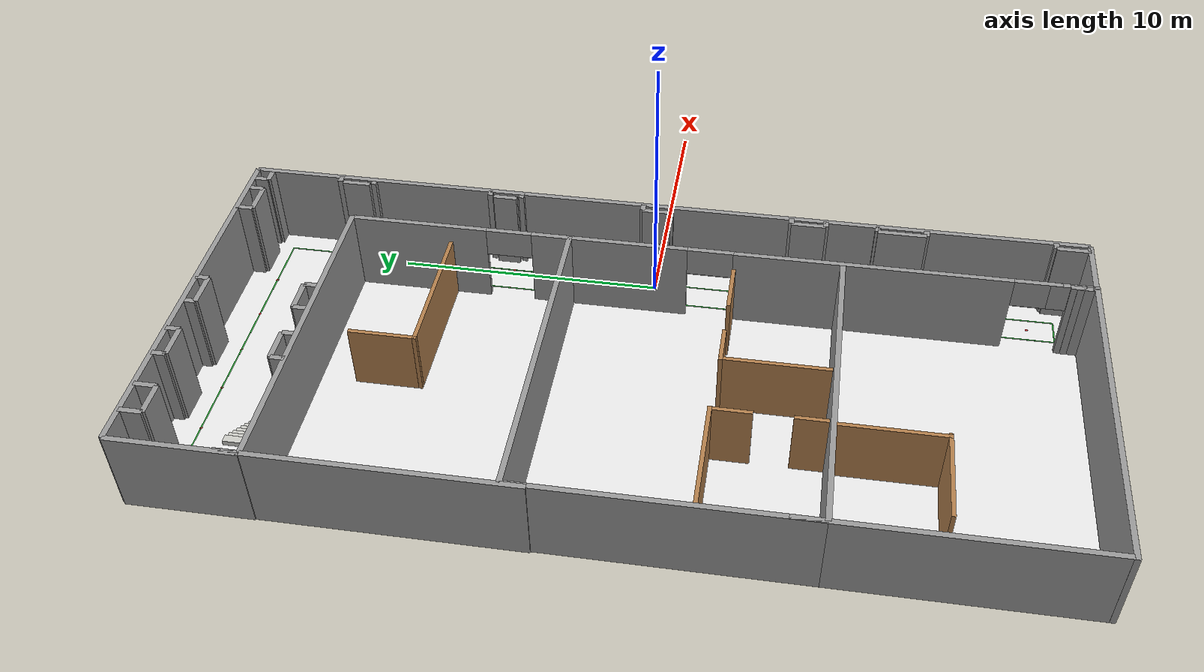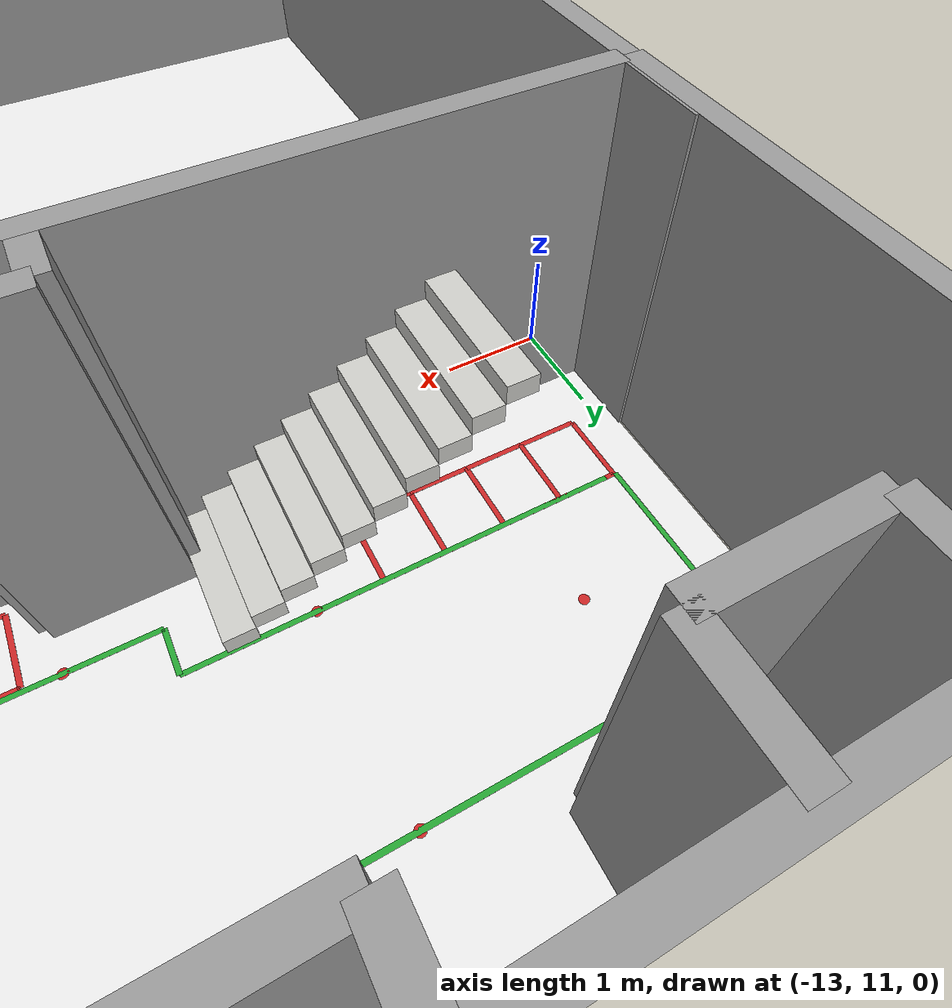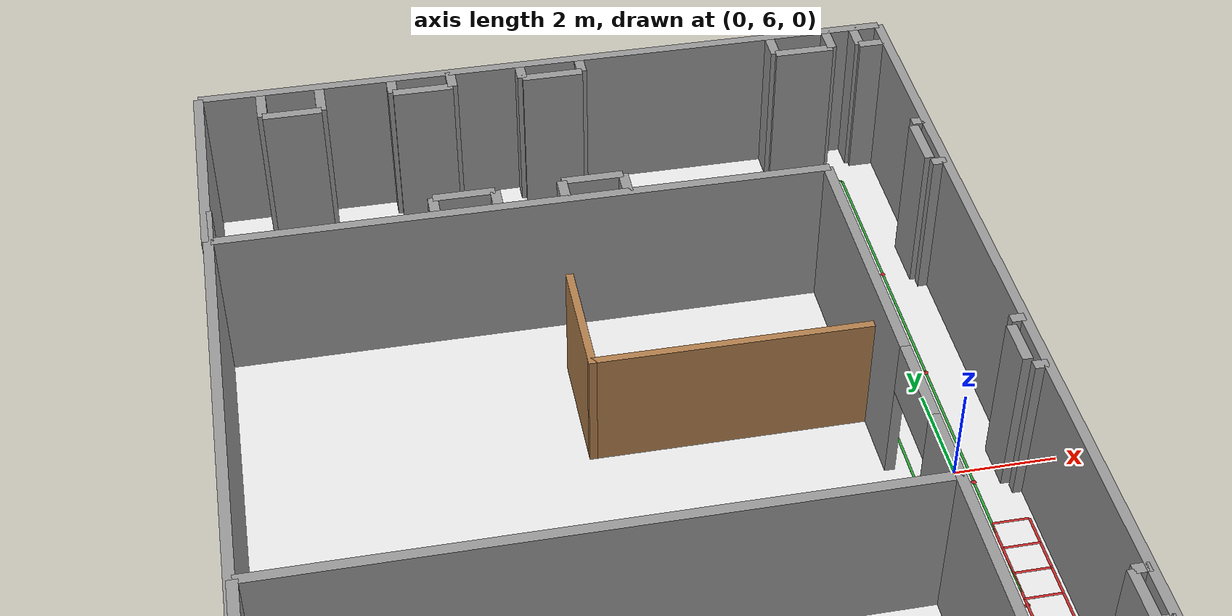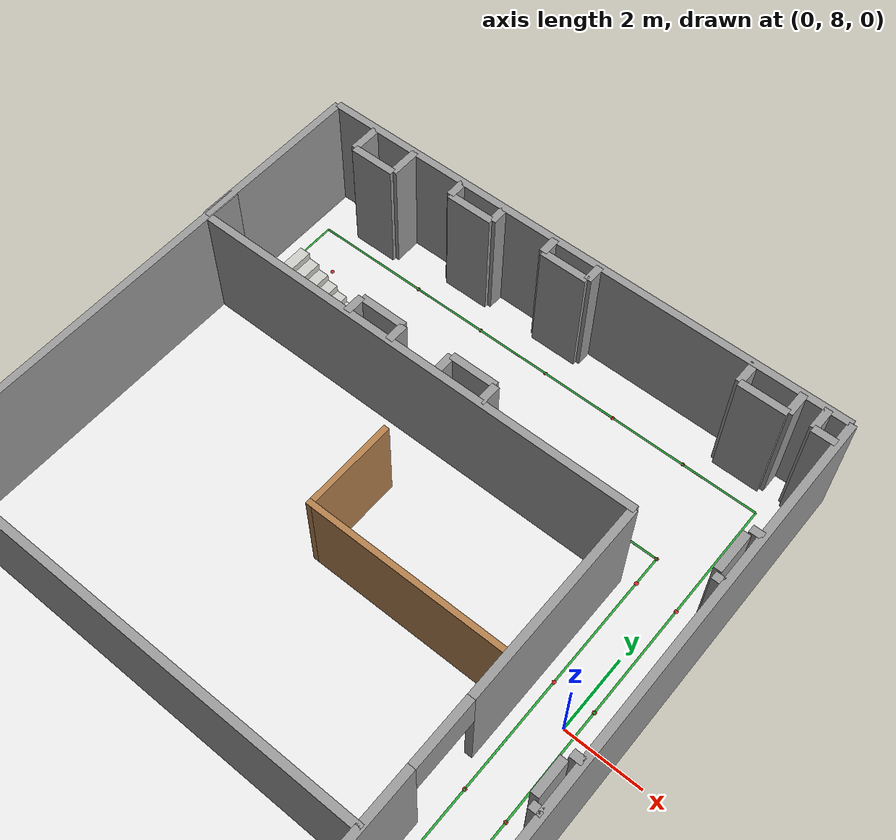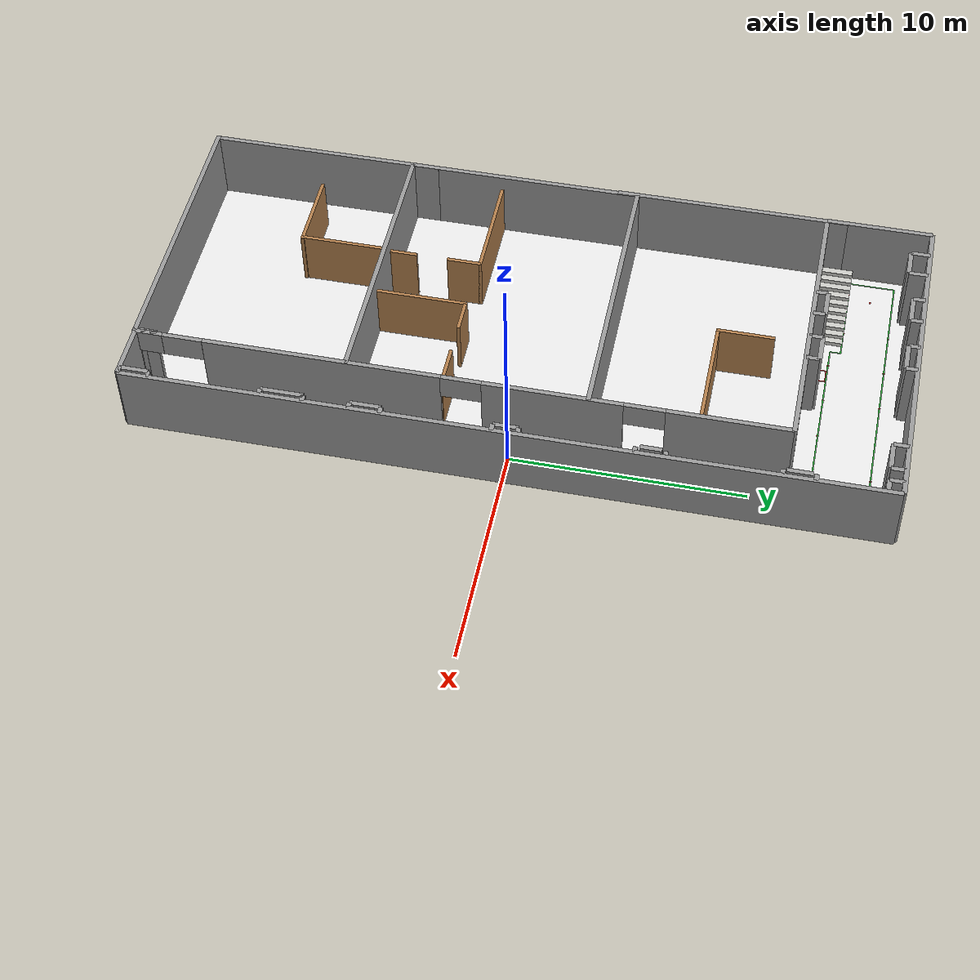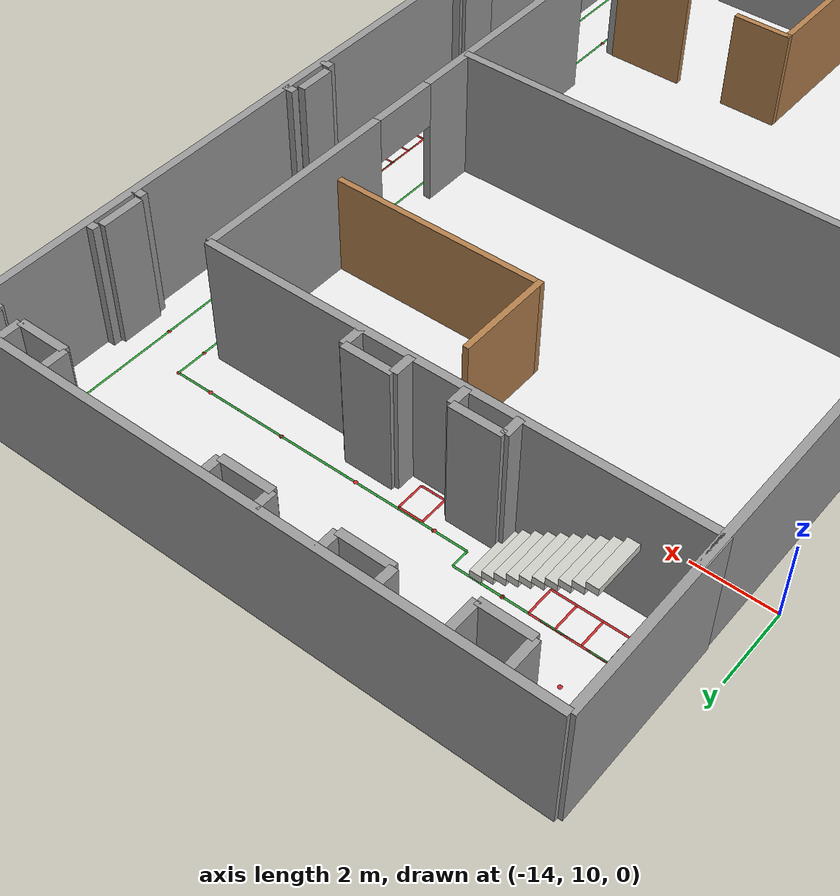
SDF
<sdf version="1.6">
 <world name="square_world">
  <spherical_coordinates>
   <surface_model>EARTH_WGS84</surface_model>
   <latitude_deg>51.9906</latitude_deg>
   <longitude_deg>4.37679</longitude_deg>
   <elevation>45.11</elevation>
   <heading_deg>180</heading_deg>
  </spherical_coordinates>
  <physics name="default_physics" default="0" type="ode">
   <max_step_size>0.001</max_step_size>
   <real_time_factor>1</real_time_factor>
   <real_time_update_rate>1000</real_time_update_rate>
  </physics>
  <gravity>0 0 -9.8</gravity>
  <scene>
   <ambient>0.4 0.4 0.4 1</ambient>
   <background>0.7 0.7 0.7 1</background>
   <shadows>0</shadows>
   <grid>0</grid>
  </scene>
  <model name="floor">
   <static>1</static>
   <pose>-5.99 0 0 0 -0 0</pose>
   <link name="link">
    <collision name="collision">
     <geometry><plane><normal>0 0 1</normal><size>14.34 32.2</size></plane></geometry>
     <surface><friction><ode><mu>100</mu><mu2>50</mu2></ode></friction></surface>
    </collision>
    <visual name="visual">
     <cast_shadows>0</cast_shadows>
     <geometry><plane><normal>0 0 1</normal><size>14.36 32.2</size></plane></geometry>
     <material><script><name>Gazebo/White</name><uri>__default__</uri></script></material>
    </visual>
    <velocity_decay><linear>0</linear><angular>0</angular></velocity_decay>
   </link>
  </model>
  <model name="wall1">
   <static>1</static>
   <pose>1.18 0 1.6 0 0 -1.5708</pose>
   <link name="wall_link">
    <inertial><mass>10000</mass></inertial>
    <collision name="wall_collision">
     <geometry><box><size>32.2 0.2 3.2</size></box></geometry>
     <surface><contact><collide_bitmask>2</collide_bitmask></contact></surface>
    </collision>
    <visual name="wall_visual">
     <geometry><box><size>32.2 0.2 3.2</size></box></geometry>
     <material><script><name>Gazebo/Grey</name><uri>__default__</uri></script></material>
    </visual>
   </link>
  </model>
  <model name="wall3">
   <static>1</static>
   <pose>-7.17 11.525 1.6 0 -0 0</pose>
   <link name="wall_link">
    <inertial><mass>10000</mass></inertial>
    <collision name="wall_collision">
     <geometry><box><size>12.07 0.2 3.2</size></box></geometry>
     <surface><contact><collide_bitmask>2</collide_bitmask></contact></surface>
    </collision>
    <visual name="wall_visual">
     <geometry><box><size>12.07 0.2 3.2</size></box></geometry>
     <material><script><name>Gazebo/Grey</name><uri>__default__</uri></script></material>
    </visual>
   </link>
  </model>
  <model name="wall4">
   <static>1</static>
   <pose>0 -16.1 1.6 0 -0 0</pose>
   <link name="wall_link">
    <inertial><mass>10000</mass></inertial>
    <collision name="wall_collision">
     <geometry><box><size>2.36 0.2 3.2</size></box></geometry>
     <surface><contact><collide_bitmask>2</collide_bitmask></contact></surface>
    </collision>
    <visual name="wall_visual">
     <geometry><box><size>2.36 0.2 3.2</size></box></geometry>
     <material><script><name>Gazebo/Grey</name><uri>__default__</uri></script></material>
    </visual>
   </link>
  </model>
  <model name="wall5">
   <static>1</static>
   <pose>-6.05 16.1 1.6 0 -0 0</pose>
   <link name="wall_link">
    <inertial><mass>10000</mass></inertial>
    <collision name="wall_collision">
     <geometry><box><size>14.46 0.2 3.2</size></box></geometry>
     <surface><contact><collide_bitmask>2</collide_bitmask></contact></surface>
    </collision>
    <visual name="wall_visual">
     <geometry><box><size>14.46 0.2 3.2</size></box></geometry>
     <material><script><name>Gazebo/Grey</name><uri>__default__</uri></script></material>
    </visual>
   </link>
  </model>
  <model name="wall6">
   <static>1</static>
   <pose>-13.28 13.8125 1.6 0 0 -1.5708</pose>
   <link name="wall_link">
    <inertial><mass>10000</mass></inertial>
    <collision name="wall_collision">
     <geometry><box><size>4.575 0.2 3.2</size></box></geometry>
     <surface><contact><collide_bitmask>2</collide_bitmask></contact></surface>
    </collision>
    <visual name="wall_visual">
     <geometry><box><size>4.575 0.2 3.2</size></box></geometry>
     <material><script><name>Gazebo/Grey</name><uri>__default__</uri></script></material>
    </visual>
   </link>
  </model>
  <model name="wall7">
   <static>1</static>
   <pose>1.0315 -16.1 1.6 0 -0 0</pose>
   <link name="wall_link">
    <inertial><mass>10000</mass></inertial>
    <collision name="wall_collision">
     <geometry><box><size>0.297 0.2 3.2</size></box></geometry>
     <surface><contact><collide_bitmask>2</collide_bitmask></contact></surface>
    </collision>
    <visual name="wall_visual">
     <geometry><box><size>0.297 0.2 3.2</size></box></geometry>
     <material><script><name>Gazebo/Grey</name><uri>__default__</uri></script></material>
    </visual>
   </link>
  </model>
  <model name="wall8">
   <static>1</static>
   <pose>1.0315 -14.86 1.6 0 -0 0</pose>
   <link name="wall_link">
    <inertial><mass>10000</mass></inertial>
    <collision name="wall_collision">
     <geometry><box><size>0.297 0.2 3.2</size></box></geometry>
     <surface><contact><collide_bitmask>2</collide_bitmask></contact></surface>
    </collision>
    <visual name="wall_visual">
     <geometry><box><size>0.297 0.2 3.2</size></box></geometry>
     <material><script><name>Gazebo/Grey</name><uri>__default__</uri></script></material>
    </visual>
   </link>
  </model>
  <model name="wall9">
   <static>1</static>
   <pose>0.883 -15.48 1.6 0 0 -1.5708</pose>
   <link name="wall_link">
    <inertial><mass>10000</mass></inertial>
    <collision name="wall_collision">
     <geometry><box><size>1.24 0.2 3.2</size></box></geometry>
     <surface><contact><collide_bitmask>2</collide_bitmask></contact></surface>
    </collision>
    <visual name="wall_visual">
     <geometry><box><size>1.24 0.2 3.2</size></box></geometry>
     <material><script><name>Gazebo/Grey</name><uri>__default__</uri></script></material>
    </visual>
   </link>
  </model>
  <model name="wall10">
   <static>1</static>
   <pose>1.035 -10.1 1.6 0 -0 0</pose>
   <link name="wall_link">
    <inertial><mass>10000</mass></inertial>
    <collision name="wall_collision">
     <geometry><box><size>0.29 0.2 3.2</size></box></geometry>
     <surface><contact><collide_bitmask>2</collide_bitmask></contact></surface>
    </collision>
    <visual name="wall_visual">
     <geometry><box><size>0.29 0.2 3.2</size></box></geometry>
     <material><script><name>Gazebo/Grey</name><uri>__default__</uri></script></material>
    </visual>
   </link>
  </model>
  <model name="wall11">
   <static>1</static>
   <pose>1.035 -8.28 1.6 0 -0 0</pose>
   <link name="wall_link">
    <inertial><mass>10000</mass></inertial>
    <collision name="wall_collision">
     <geometry><box><size>0.29 0.2 3.2</size></box></geometry>
     <surface><contact><collide_bitmask>2</collide_bitmask></contact></surface>
    </collision>
    <visual name="wall_visual">
     <geometry><box><size>0.29 0.2 3.2</size></box></geometry>
     <material><script><name>Gazebo/Grey</name><uri>__default__</uri></script></material>
    </visual>
   </link>
  </model>
  <model name="wall12">
   <static>1</static>
   <pose>0.89 -9.19 1.6 0 0 -1.5708</pose>
   <link name="wall_link">
    <inertial><mass>10000</mass></inertial>
    <collision name="wall_collision">
     <geometry><box><size>1.82 0.2 3.2</size></box></geometry>
     <surface><contact><collide_bitmask>2</collide_bitmask></contact></surface>
    </collision>
    <visual name="wall_visual">
     <geometry><box><size>1.82 0.2 3.2</size></box></geometry>
     <material><script><name>Gazebo/Grey</name><uri>__default__</uri></script></material>
    </visual>
   </link>
  </model>
  <model name="wall13">
   <static>1</static>
   <pose>1.0365 -6.34 1.6 0 -0 0</pose>
   <link name="wall_link">
    <inertial><mass>10000</mass></inertial>
    <collision name="wall_collision">
     <geometry><box><size>0.287 0.2 3.2</size></box></geometry>
     <surface><contact><collide_bitmask>2</collide_bitmask></contact></surface>
    </collision>
    <visual name="wall_visual">
     <geometry><box><size>0.287 0.2 3.2</size></box></geometry>
     <material><script><name>Gazebo/Grey</name><uri>__default__</uri></script></material>
    </visual>
   </link>
  </model>
  <model name="wall14">
   <static>1</static>
   <pose>1.0365 -5.03 1.6 0 -0 0</pose>
   <link name="wall_link">
    <inertial><mass>10000</mass></inertial>
    <collision name="wall_collision">
     <geometry><box><size>0.287 0.2 3.2</size></box></geometry>
     <surface><contact><collide_bitmask>2</collide_bitmask></contact></surface>
    </collision>
    <visual name="wall_visual">
     <geometry><box><size>0.287 0.2 3.2</size></box></geometry>
     <material><script><name>Gazebo/Grey</name><uri>__default__</uri></script></material>
    </visual>
   </link>
  </model>
  <model name="wall15">
   <static>1</static>
   <pose>0.893 -5.685 1.6 0 0 -1.5708</pose>
   <link name="wall_link">
    <inertial><mass>10000</mass></inertial>
    <collision name="wall_collision">
     <geometry><box><size>1.31 0.2 3.2</size></box></geometry>
     <surface><contact><collide_bitmask>2</collide_bitmask></contact></surface>
    </collision>
    <visual name="wall_visual">
     <geometry><box><size>1.31 0.2 3.2</size></box></geometry>
     <material><script><name>Gazebo/Grey</name><uri>__default__</uri></script></material>
    </visual>
   </link>
  </model>
  <model name="wall16">
   <static>1</static>
   <pose>1.0195 -0.42 1.6 0 -0 0</pose>
   <link name="wall_link">
    <inertial><mass>10000</mass></inertial>
    <collision name="wall_collision">
     <geometry><box><size>0.321 0.2 3.2</size></box></geometry>
     <surface><contact><collide_bitmask>2</collide_bitmask></contact></surface>
    </collision>
    <visual name="wall_visual">
     <geometry><box><size>0.321 0.2 3.2</size></box></geometry>
     <material><script><name>Gazebo/Grey</name><uri>__default__</uri></script></material>
    </visual>
   </link>
  </model>
  <model name="wall17">
   <static>1</static>
   <pose>1.0195 0.65 1.6 0 -0 0</pose>
   <link name="wall_link">
    <inertial><mass>10000</mass></inertial>
    <collision name="wall_collision">
     <geometry><box><size>0.321 0.2 3.2</size></box></geometry>
     <surface><contact><collide_bitmask>2</collide_bitmask></contact></surface>
    </collision>
    <visual name="wall_visual">
     <geometry><box><size>0.321 0.2 3.2</size></box></geometry>
     <material><script><name>Gazebo/Grey</name><uri>__default__</uri></script></material>
    </visual>
   </link>
  </model>
  <model name="wall18">
   <static>1</static>
   <pose>0.859 0.115 1.6 0 0 -1.5708</pose>
   <link name="wall_link">
    <inertial><mass>10000</mass></inertial>
    <collision name="wall_collision">
     <geometry><box><size>1.07 0.2 3.2</size></box></geometry>
     <surface><contact><collide_bitmask>2</collide_bitmask></contact></surface>
    </collision>
    <visual name="wall_visual">
     <geometry><box><size>1.07 0.2 3.2</size></box></geometry>
     <material><script><name>Gazebo/Grey</name><uri>__default__</uri></script></material>
    </visual>
   </link>
  </model>
  <model name="wall19">
   <static>1</static>
   <pose>1.04 5.41 1.6 0 -0 0</pose>
   <link name="wall_link">
    <inertial><mass>10000</mass></inertial>
    <collision name="wall_collision">
     <geometry><box><size>0.28 0.2 3.2</size></box></geometry>
     <surface><contact><collide_bitmask>2</collide_bitmask></contact></surface>
    </collision>
    <visual name="wall_visual">
     <geometry><box><size>0.28 0.2 3.2</size></box></geometry>
     <material><script><name>Gazebo/Grey</name><uri>__default__</uri></script></material>
    </visual>
   </link>
  </model>
  <model name="wall20">
   <static>1</static>
   <pose>1.04 6.64 1.6 0 -0 0</pose>
   <link name="wall_link">
    <inertial><mass>10000</mass></inertial>
    <collision name="wall_collision">
     <geometry><box><size>0.28 0.2 3.2</size></box></geometry>
     <surface><contact><collide_bitmask>2</collide_bitmask></contact></surface>
    </collision>
    <visual name="wall_visual">
     <geometry><box><size>0.28 0.2 3.2</size></box></geometry>
     <material><script><name>Gazebo/Grey</name><uri>__default__</uri></script></material>
    </visual>
   </link>
  </model>
  <model name="wall21">
   <static>1</static>
   <pose>0.859 6.025 1.6 0 0 -1.5708</pose>
   <link name="wall_link">
    <inertial><mass>10000</mass></inertial>
    <collision name="wall_collision">
     <geometry><box><size>0.9 0.2 3.2</size></box></geometry>
     <surface><contact><collide_bitmask>2</collide_bitmask></contact></surface>
    </collision>
    <visual name="wall_visual">
     <geometry><box><size>0.9 0.2 3.2</size></box></geometry>
     <material><script><name>Gazebo/Grey</name><uri>__default__</uri></script></material>
    </visual>
   </link>
  </model>
  <model name="wall22">
   <static>1</static>
   <pose>1.0315 11.31 1.6 0 -0 0</pose>
   <link name="wall_link">
    <inertial><mass>10000</mass></inertial>
    <collision name="wall_collision">
     <geometry><box><size>0.297 0.2 3.2</size></box></geometry>
     <surface><contact><collide_bitmask>2</collide_bitmask></contact></surface>
    </collision>
    <visual name="wall_visual">
     <geometry><box><size>0.297 0.2 3.2</size></box></geometry>
     <material><script><name>Gazebo/Grey</name><uri>__default__</uri></script></material>
    </visual>
   </link>
  </model>
  <model name="wall23">
   <static>1</static>
   <pose>1.0315 12.65 1.6 0 -0 0</pose>
   <link name="wall_link">
    <inertial><mass>10000</mass></inertial>
    <collision name="wall_collision">
     <geometry><box><size>0.297 0.2 3.2</size></box></geometry>
     <surface><contact><collide_bitmask>2</collide_bitmask></contact></surface>
    </collision>
    <visual name="wall_visual">
     <geometry><box><size>0.297 0.2 3.2</size></box></geometry>
     <material><script><name>Gazebo/Grey</name><uri>__default__</uri></script></material>
    </visual>
   </link>
  </model>
  <model name="wall24">
   <static>1</static>
   <pose>0.883 11.98 1.6 0 0 -1.5708</pose>
   <link name="wall_link">
    <inertial><mass>10000</mass></inertial>
    <collision name="wall_collision">
     <geometry><box><size>1.07 0.2 3.2</size></box></geometry>
     <surface><contact><collide_bitmask>2</collide_bitmask></contact></surface>
    </collision>
    <visual name="wall_visual">
     <geometry><box><size>1.07 0.2 3.2</size></box></geometry>
     <material><script><name>Gazebo/Grey</name><uri>__default__</uri></script></material>
    </visual>
   </link>
  </model>
  <model name="wall25">
   <static>1</static>
   <pose>0.87 15.48 1.6 0 -0 0</pose>
   <link name="wall_link">
    <inertial><mass>10000</mass></inertial>
    <collision name="wall_collision">
     <geometry><box><size>0.58 0.2 3.2</size></box></geometry>
     <surface><contact><collide_bitmask>2</collide_bitmask></contact></surface>
    </collision>
    <visual name="wall_visual">
     <geometry><box><size>0.58 0.2 3.2</size></box></geometry>
     <material><script><name>Gazebo/Grey</name><uri>__default__</uri></script></material>
    </visual>
   </link>
  </model>
  <model name="wall26">
   <static>1</static>
   <pose>0.6 15.79 1.6 0 0 -1.5708</pose>
   <link name="wall_link">
    <inertial><mass>10000</mass></inertial>
    <collision name="wall_collision">
     <geometry><box><size>0.62 0.2 3.2</size></box></geometry>
     <surface><contact><collide_bitmask>2</collide_bitmask></contact></surface>
    </collision>
    <visual name="wall_visual">
     <geometry><box><size>0.62 0.2 3.2</size></box></geometry>
     <material><script><name>Gazebo/Grey</name><uri>__default__</uri></script></material>
    </visual>
   </link>
  </model>
  <model name="wall27">
   <static>1</static>
   <pose>-0.01 15.787 1.6 0 0 -1.5708</pose>
   <link name="wall_link">
    <inertial><mass>10000</mass></inertial>
    <collision name="wall_collision">
     <geometry><box><size>0.626 0.2 3.2</size></box></geometry>
     <surface><contact><collide_bitmask>2</collide_bitmask></contact></surface>
    </collision>
    <visual name="wall_visual">
     <geometry><box><size>0.626 0.2 3.2</size></box></geometry>
     <material><script><name>Gazebo/Grey</name><uri>__default__</uri></script></material>
    </visual>
   </link>
  </model>
  <model name="wall28">
   <static>1</static>
   <pose>-1.24 15.787 1.6 0 0 -1.5708</pose>
   <link name="wall_link">
    <inertial><mass>10000</mass></inertial>
    <collision name="wall_collision">
     <geometry><box><size>0.626 0.2 3.2</size></box></geometry>
     <surface><contact><collide_bitmask>2</collide_bitmask></contact></surface>
    </collision>
    <visual name="wall_visual">
     <geometry><box><size>0.626 0.2 3.2</size></box></geometry>
     <material><script><name>Gazebo/Grey</name><uri>__default__</uri></script></material>
    </visual>
   </link>
  </model>
  <model name="wall29">
   <static>1</static>
   <pose>-0.625 15.474 1.6 0 -0 0</pose>
   <link name="wall_link">
    <inertial><mass>10000</mass></inertial>
    <collision name="wall_collision">
     <geometry><box><size>1.23 0.2 3.2</size></box></geometry>
     <surface><contact><collide_bitmask>2</collide_bitmask></contact></surface>
    </collision>
    <visual name="wall_visual">
     <geometry><box><size>1.23 0.2 3.2</size></box></geometry>
     <material><script><name>Gazebo/Grey</name><uri>__default__</uri></script></material>
    </visual>
   </link>
  </model>
  <model name="wall30">
   <static>1</static>
   <pose>-5.37 15.86 1.6 0 0 -1.5708</pose>
   <link name="wall_link">
    <inertial><mass>10000</mass></inertial>
    <collision name="wall_collision">
     <geometry><box><size>0.48 0.2 3.2</size></box></geometry>
     <surface><contact><collide_bitmask>2</collide_bitmask></contact></surface>
    </collision>
    <visual name="wall_visual">
     <geometry><box><size>0.48 0.2 3.2</size></box></geometry>
     <material><script><name>Gazebo/Grey</name><uri>__default__</uri></script></material>
    </visual>
   </link>
  </model>
  <model name="wall31">
   <static>1</static>
   <pose>-6.63 15.86 1.6 0 0 -1.5708</pose>
   <link name="wall_link">
    <inertial><mass>10000</mass></inertial>
    <collision name="wall_collision">
     <geometry><box><size>0.48 0.2 3.2</size></box></geometry>
     <surface><contact><collide_bitmask>2</collide_bitmask></contact></surface>
    </collision>
    <visual name="wall_visual">
     <geometry><box><size>0.48 0.2 3.2</size></box></geometry>
     <material><script><name>Gazebo/Grey</name><uri>__default__</uri></script></material>
    </visual>
   </link>
  </model>
  <model name="wall32">
   <static>1</static>
   <pose>-6 15.62 1.6 0 -0 0</pose>
   <link name="wall_link">
    <inertial><mass>10000</mass></inertial>
    <collision name="wall_collision">
     <geometry><box><size>1.26 0.2 3.2</size></box></geometry>
     <surface><contact><collide_bitmask>2</collide_bitmask></contact></surface>
    </collision>
    <visual name="wall_visual">
     <geometry><box><size>1.26 0.2 3.2</size></box></geometry>
     <material><script><name>Gazebo/Grey</name><uri>__default__</uri></script></material>
    </visual>
   </link>
  </model>
  <model name="wall33">
   <static>1</static>
   <pose>-8.09 15.85 1.6 0 0 -1.5708</pose>
   <link name="wall_link">
    <inertial><mass>10000</mass></inertial>
    <collision name="wall_collision">
     <geometry><box><size>0.5 0.2 3.2</size></box></geometry>
     <surface><contact><collide_bitmask>2</collide_bitmask></contact></surface>
    </collision>
    <visual name="wall_visual">
     <geometry><box><size>0.5 0.2 3.2</size></box></geometry>
     <material><script><name>Gazebo/Grey</name><uri>__default__</uri></script></material>
    </visual>
   </link>
  </model>
  <model name="wall34">
   <static>1</static>
   <pose>-9.33 15.85 1.6 0 0 -1.5708</pose>
   <link name="wall_link">
    <inertial><mass>10000</mass></inertial>
    <collision name="wall_collision">
     <geometry><box><size>0.5 0.2 3.2</size></box></geometry>
     <surface><contact><collide_bitmask>2</collide_bitmask></contact></surface>
    </collision>
    <visual name="wall_visual">
     <geometry><box><size>0.5 0.2 3.2</size></box></geometry>
     <material><script><name>Gazebo/Grey</name><uri>__default__</uri></script></material>
    </visual>
   </link>
  </model>
  <model name="wall35">
   <static>1</static>
   <pose>-8.71 15.6 1.6 0 -0 0</pose>
   <link name="wall_link">
    <inertial><mass>10000</mass></inertial>
    <collision name="wall_collision">
     <geometry><box><size>1.24 0.2 3.2</size></box></geometry>
     <surface><contact><collide_bitmask>2</collide_bitmask></contact></surface>
    </collision>
    <visual name="wall_visual">
     <geometry><box><size>1.24 0.2 3.2</size></box></geometry>
     <material><script><name>Gazebo/Grey</name><uri>__default__</uri></script></material>
    </visual>
   </link>
  </model>
  <model name="wall36">
   <static>1</static>
   <pose>-10.82 15.69 1.6 0 0 -1.5708</pose>
   <link name="wall_link">
    <inertial><mass>10000</mass></inertial>
    <collision name="wall_collision">
     <geometry><box><size>0.82 0.2 3.2</size></box></geometry>
     <surface><contact><collide_bitmask>2</collide_bitmask></contact></surface>
    </collision>
    <visual name="wall_visual">
     <geometry><box><size>0.82 0.2 3.2</size></box></geometry>
     <material><script><name>Gazebo/Grey</name><uri>__default__</uri></script></material>
    </visual>
   </link>
  </model>
  <model name="wall37">
   <static>1</static>
   <pose>-12.02 15.69 1.6 0 0 -1.5708</pose>
   <link name="wall_link">
    <inertial><mass>10000</mass></inertial>
    <collision name="wall_collision">
     <geometry><box><size>0.82 0.2 3.2</size></box></geometry>
     <surface><contact><collide_bitmask>2</collide_bitmask></contact></surface>
    </collision>
    <visual name="wall_visual">
     <geometry><box><size>0.82 0.2 3.2</size></box></geometry>
     <material><script><name>Gazebo/Grey</name><uri>__default__</uri></script></material>
    </visual>
   </link>
  </model>
  <model name="wall38">
   <static>1</static>
   <pose>-11.42 15.28 1.6 0 -0 0</pose>
   <link name="wall_link">
    <inertial><mass>10000</mass></inertial>
    <collision name="wall_collision">
     <geometry><box><size>1.2 0.2 3.2</size></box></geometry>
     <surface><contact><collide_bitmask>2</collide_bitmask></contact></surface>
    </collision>
    <visual name="wall_visual">
     <geometry><box><size>1.2 0.2 3.2</size></box></geometry>
     <material><script><name>Gazebo/Grey</name><uri>__default__</uri></script></material>
    </visual>
   </link>
  </model>
  <model name="wall39">
   <static>1</static>
   <pose>-5.18 11.8025 1.6 0 0 -1.5708</pose>
   <link name="wall_link">
    <inertial><mass>10000</mass></inertial>
    <collision name="wall_collision">
     <geometry><box><size>0.555 0.2 3.2</size></box></geometry>
     <surface><contact><collide_bitmask>2</collide_bitmask></contact></surface>
    </collision>
    <visual name="wall_visual">
     <geometry><box><size>0.555 0.2 3.2</size></box></geometry>
     <material><script><name>Gazebo/Grey</name><uri>__default__</uri></script></material>
    </visual>
   </link>
  </model>
  <model name="wall40">
   <static>1</static>
   <pose>-6.4 11.8025 1.6 0 0 -1.5708</pose>
   <link name="wall_link">
    <inertial><mass>10000</mass></inertial>
    <collision name="wall_collision">
     <geometry><box><size>0.555 0.2 3.2</size></box></geometry>
     <surface><contact><collide_bitmask>2</collide_bitmask></contact></surface>
    </collision>
    <visual name="wall_visual">
     <geometry><box><size>0.555 0.2 3.2</size></box></geometry>
     <material><script><name>Gazebo/Grey</name><uri>__default__</uri></script></material>
    </visual>
   </link>
  </model>
  <model name="wall41">
   <static>1</static>
   <pose>-5.79 12.08 1.6 0 -0 0</pose>
   <link name="wall_link">
    <inertial><mass>10000</mass></inertial>
    <collision name="wall_collision">
     <geometry><box><size>1.22 0.2 3.2</size></box></geometry>
     <surface><contact><collide_bitmask>2</collide_bitmask></contact></surface>
    </collision>
    <visual name="wall_visual">
     <geometry><box><size>1.22 0.2 3.2</size></box></geometry>
     <material><script><name>Gazebo/Grey</name><uri>__default__</uri></script></material>
    </visual>
   </link>
  </model>
  <model name="wall42">
   <static>1</static>
   <pose>-7.72 11.7775 1.6 0 0 -1.5708</pose>
   <link name="wall_link">
    <inertial><mass>10000</mass></inertial>
    <collision name="wall_collision">
     <geometry><box><size>0.505 0.2 3.2</size></box></geometry>
     <surface><contact><collide_bitmask>2</collide_bitmask></contact></surface>
    </collision>
    <visual name="wall_visual">
     <geometry><box><size>0.505 0.2 3.2</size></box></geometry>
     <material><script><name>Gazebo/Grey</name><uri>__default__</uri></script></material>
    </visual>
   </link>
  </model>
  <model name="wall43">
   <static>1</static>
   <pose>-8.94 11.7775 1.6 0 0 -1.5708</pose>
   <link name="wall_link">
    <inertial><mass>10000</mass></inertial>
    <collision name="wall_collision">
     <geometry><box><size>0.505 0.2 3.2</size></box></geometry>
     <surface><contact><collide_bitmask>2</collide_bitmask></contact></surface>
    </collision>
    <visual name="wall_visual">
     <geometry><box><size>0.505 0.2 3.2</size></box></geometry>
     <material><script><name>Gazebo/Grey</name><uri>__default__</uri></script></material>
    </visual>
   </link>
  </model>
  <model name="wall44">
   <static>1</static>
   <pose>-8.33 12.03 1.6 0 -0 0</pose>
   <link name="wall_link">
    <inertial><mass>10000</mass></inertial>
    <collision name="wall_collision">
     <geometry><box><size>1.22 0.2 3.2</size></box></geometry>
     <surface><contact><collide_bitmask>2</collide_bitmask></contact></surface>
    </collision>
    <visual name="wall_visual">
     <geometry><box><size>1.22 0.2 3.2</size></box></geometry>
     <material><script><name>Gazebo/Grey</name><uri>__default__</uri></script></material>
    </visual>
   </link>
  </model>
  <model name="wall46">
   <static>1</static>
   <pose>-1.18 1.62 1.6 0 0 -1.5708</pose>
   <link name="wall_link">
    <inertial><mass>10000</mass></inertial>
    <collision name="wall_collision">
     <geometry><box><size>5.9 0.2 3.2</size></box></geometry>
     <surface><contact><collide_bitmask>2</collide_bitmask></contact></surface>
    </collision>
    <visual name="wall_visual">
     <geometry><box><size>5.9 0.2 3.2</size></box></geometry>
     <material><script><name>Gazebo/Grey</name><uri>__default__</uri></script></material>
    </visual>
   </link>
  </model>
  <model name="wall47">
   <static>1</static>
   <pose>-1.18 8.91 1.6 0 0 -1.5708</pose>
   <link name="wall_link">
    <inertial><mass>10000</mass></inertial>
    <collision name="wall_collision">
     <geometry><box><size>5.22 0.2 3.2</size></box></geometry>
     <surface><contact><collide_bitmask>2</collide_bitmask></contact></surface>
    </collision>
    <visual name="wall_visual">
     <geometry><box><size>5.22 0.2 3.2</size></box></geometry>
     <material><script><name>Gazebo/Grey</name><uri>__default__</uri></script></material>
    </visual>
   </link>
  </model>
  <model name="wall48">
   <static>1</static>
   <pose>-7.17 3.12 1.6 0 -0 0</pose>
   <link name="wall_link">
    <inertial><mass>10000</mass></inertial>
    <collision name="wall_collision">
     <geometry><box><size>12.07 0.2 3.2</size></box></geometry>
     <surface><contact><collide_bitmask>2</collide_bitmask></contact></surface>
    </collision>
    <visual name="wall_visual">
     <geometry><box><size>12.07 0.2 3.2</size></box></geometry>
     <material><script><name>Gazebo/Grey</name><uri>__default__</uri></script></material>
    </visual>
   </link>
  </model>
  <model name="wall49">
   <static>1</static>
   <pose>-13.205 -1.97 1.6 0 0 -1.5708</pose>
   <link name="wall_link">
    <inertial><mass>10000</mass></inertial>
    <collision name="wall_collision">
     <geometry><box><size>10.18 0.2 3.2</size></box></geometry>
     <surface><contact><collide_bitmask>2</collide_bitmask></contact></surface>
    </collision>
    <visual name="wall_visual">
     <geometry><box><size>10.18 0.2 3.2</size></box></geometry>
     <material><script><name>Gazebo/Grey</name><uri>__default__</uri></script></material>
    </visual>
   </link>
  </model>
  <model name="wall50">
   <static>1</static>
   <pose>-7.17 -7.06 1.6 0 -0 0</pose>
   <link name="wall_link">
    <inertial><mass>10000</mass></inertial>
    <collision name="wall_collision">
     <geometry><box><size>12.07 0.2 3.2</size></box></geometry>
     <surface><contact><collide_bitmask>2</collide_bitmask></contact></surface>
    </collision>
    <visual name="wall_visual">
     <geometry><box><size>12.07 0.2 3.2</size></box></geometry>
     <material><script><name>Gazebo/Grey</name><uri>__default__</uri></script></material>
    </visual>
   </link>
  </model>
  <model name="Stairs">
   <pose>-10.345 12.23 0 0 -0 0</pose>
   <link name="Stairs_1">
    <visual name="Stairs_1_Visual_0">
     <pose>1.2645 0 0.0935 0 0 -1.5708</pose>
     <geometry><box><size>1.41 0.281 0.187</size></box></geometry>
     <material>
      <script><uri>file://media/materials/scripts/gazebo.material</uri><name>Gazebo/CeilingTiled</name></script>
      <ambient>0.760784 0.662745 0.627451 1</ambient>
     </material>
    </visual>
    <collision name="Stairs_1_Collision_0">
     <geometry><box><size>1.41 0.281 0.187</size></box></geometry>
     <pose>1.2645 0 0.0935 0 0 -1.5708</pose>
    </collision>
    <visual name="Stairs_1_Visual_1">
     <pose>0.9835 0 0.2805 0 0 -1.5708</pose>
     <geometry><box><size>1.41 0.281 0.187</size></box></geometry>
     <material>
      <script><uri>file://media/materials/scripts/gazebo.material</uri><name>Gazebo/CeilingTiled</name></script>
      <ambient>0.760784 0.662745 0.627451 1</ambient>
     </material>
    </visual>
    <collision name="Stairs_1_Collision_1">
     <geometry><box><size>1.41 0.281 0.187</size></box></geometry>
     <pose>0.9835 0 0.2805 0 0 -1.5708</pose>
    </collision>
    <visual name="Stairs_1_Visual_2">
     <pose>0.7025 0 0.4675 0 0 -1.5708</pose>
     <geometry><box><size>1.41 0.281 0.187</size></box></geometry>
     <material>
      <script><uri>file://media/materials/scripts/gazebo.material</uri><name>Gazebo/CeilingTiled</name></script>
      <ambient>0.760784 0.662745 0.627451 1</ambient>
     </material>
    </visual>
    <collision name="Stairs_1_Collision_2">
     <geometry><box><size>1.41 0.281 0.187</size></box></geometry>
     <pose>0.7025 0 0.4675 0 0 -1.5708</pose>
    </collision>
    <visual name="Stairs_1_Visual_3">
     <pose>0.4215 0 0.6545 0 0 -1.5708</pose>
     <geometry><box><size>1.41 0.281 0.187</size></box></geometry>
     <material>
      <script><uri>file://media/materials/scripts/gazebo.material</uri><name>Gazebo/CeilingTiled</name></script>
      <ambient>0.760784 0.662745 0.627451 1</ambient>
     </material>
    </visual>
    <collision name="Stairs_1_Collision_3">
     <geometry><box><size>1.41 0.281 0.187</size></box></geometry>
     <pose>0.4215 0 0.6545 0 0 -1.5708</pose>
    </collision>
    <visual name="Stairs_1_Visual_4">
     <pose>0.1405 0 0.8415 0 0 -1.5708</pose>
     <geometry><box><size>1.41 0.281 0.187</size></box></geometry>
     <material>
      <script><uri>file://media/materials/scripts/gazebo.material</uri><name>Gazebo/CeilingTiled</name></script>
      <ambient>0.760784 0.662745 0.627451 1</ambient>
     </material>
    </visual>
    <collision name="Stairs_1_Collision_4">
     <geometry><box><size>1.41 0.281 0.187</size></box></geometry>
     <pose>0.1405 0 0.8415 0 0 -1.5708</pose>
    </collision>
    <visual name="Stairs_1_Visual_5">
     <pose>-0.1405 0 1.0285 0 0 -1.5708</pose>
     <geometry><box><size>1.41 0.281 0.187</size></box></geometry>
     <material>
      <script><uri>file://media/materials/scripts/gazebo.material</uri><name>Gazebo/CeilingTiled</name></script>
      <ambient>0.760784 0.662745 0.627451 1</ambient>
     </material>
    </visual>
    <collision name="Stairs_1_Collision_5">
     <geometry><box><size>1.41 0.281 0.187</size></box></geometry>
     <pose>-0.1405 0 1.0285 0 0 -1.5708</pose>
    </collision>
    <visual name="Stairs_1_Visual_6">
     <pose>-0.4215 0 1.2155 0 0 -1.5708</pose>
     <geometry><box><size>1.41 0.281 0.187</size></box></geometry>
     <material>
      <script><uri>file://media/materials/scripts/gazebo.material</uri><name>Gazebo/CeilingTiled</name></script>
      <ambient>0.760784 0.662745 0.627451 1</ambient>
     </material>
    </visual>
    <collision name="Stairs_1_Collision_6">
     <geometry><box><size>1.41 0.281 0.187</size></box></geometry>
     <pose>-0.4215 0 1.2155 0 0 -1.5708</pose>
    </collision>
    <visual name="Stairs_1_Visual_7">
     <pose>-0.7025 0 1.4025 0 0 -1.5708</pose>
     <geometry><box><size>1.41 0.281 0.187</size></box></geometry>
     <material>
      <script><uri>file://media/materials/scripts/gazebo.material</uri><name>Gazebo/CeilingTiled</name></script>
      <ambient>0.760784 0.662745 0.627451 1</ambient>
     </material>
    </visual>
    <collision name="Stairs_1_Collision_7">
     <geometry><box><size>1.41 0.281 0.187</size></box></geometry>
     <pose>-0.7025 0 1.4025 0 0 -1.5708</pose>
    </collision>
    <visual name="Stairs_1_Visual_8">
     <pose>-0.9835 0 1.5895 0 0 -1.5708</pose>
     <geometry><box><size>1.41 0.281 0.187</size></box></geometry>
     <material>
      <script><uri>file://media/materials/scripts/gazebo.material</uri><name>Gazebo/CeilingTiled</name></script>
      <ambient>0.760784 0.662745 0.627451 1</ambient>
     </material>
    </visual>
    <collision name="Stairs_1_Collision_8">
     <geometry><box><size>1.41 0.281 0.187</size></box></geometry>
     <pose>-0.9835 0 1.5895 0 0 -1.5708</pose>
    </collision>
    <visual name="Stairs_1_Visual_9">
     <pose>-1.2645 0 1.7765 0 0 -1.5708</pose>
     <geometry><box><size>1.41 0.281 0.187</size></box></geometry>
     <material>
      <script><uri>file://media/materials/scripts/gazebo.material</uri><name>Gazebo/CeilingTiled</name></script>
      <ambient>0.760784 0.662745 0.627451 1</ambient>
     </material>
    </visual>
    <collision name="Stairs_1_Collision_9">
     <geometry><box><size>1.41 0.281 0.187</size></box></geometry>
     <pose>-1.2645 0 1.7765 0 0 -1.5708</pose>
    </collision>
   </link>
   <static>1</static>
  </model>
  <model name="wall488">
   <static>1</static>
   <pose>-1.18 -2.195 2.6425 0 0 -1.5708</pose>
   <link name="wall_link">
    <inertial><mass>10000</mass></inertial>
    <collision name="wall_collision">
     <geometry><box><size>1.73 0.2 1.115</size></box></geometry>
     <surface><contact><collide_bitmask>2</collide_bitmask></contact></surface>
    </collision>
    <visual name="wall_visual">
     <geometry><box><size>1.73 0.2 1.115</size></box></geometry>
     <material><script><name>Gazebo/Grey</name><uri>__default__</uri></script></material>
    </visual>
   </link>
  </model>
  <model name="wall498">
   <static>1</static>
   <pose>-1.18 5.435 2.6425 0 0 -1.5708</pose>
   <link name="wall_link">
    <inertial><mass>10000</mass></inertial>
    <collision name="wall_collision">
     <geometry><box><size>1.73 0.2 1.115</size></box></geometry>
     <surface><contact><collide_bitmask>2</collide_bitmask></contact></surface>
    </collision>
    <visual name="wall_visual">
     <geometry><box><size>1.73 0.2 1.115</size></box></geometry>
     <material><script><name>Gazebo/Grey</name><uri>__default__</uri></script></material>
    </visual>
   </link>
  </model>
  <model name="wall508">
   <static>1</static>
   <pose>-0.78 -1.41 0 0 0 -1.5708</pose>
   <link name="wall_link">
    <inertial><mass>10000</mass></inertial>
    <collision name="wall_collision">
     <geometry><box><size>27.78 0.05 0.001</size></box></geometry>
     <surface><contact><collide_bitmask>2</collide_bitmask></contact></surface>
    </collision>
    <visual name="wall_visual">
     <geometry><box><size>27.78 0.05 0.001</size></box></geometry>
     <material><script><name>Gazebo/Green</name><uri>__default__</uri></script></material>
    </visual>
   </link>
  </model>
  <model name="wall518">
   <static>1</static>
   <pose>0.28 -0.21 0 0 0 -1.5708</pose>
   <link name="wall_link">
    <inertial><mass>10000</mass></inertial>
    <collision name="wall_collision">
     <geometry><box><size>30.18 0.05 0.001</size></box></geometry>
     <surface><contact><collide_bitmask>2</collide_bitmask></contact></surface>
    </collision>
    <visual name="wall_visual">
     <geometry><box><size>30.18 0.05 0.001</size></box></geometry>
     <material><script><name>Gazebo/Green</name><uri>__default__</uri></script></material>
    </visual>
   </link>
  </model>
  <model name="wall528">
   <static>1</static>
   <pose>-0.25 -15.3 0 0 -0 0</pose>
   <link name="wall_link">
    <inertial><mass>10000</mass></inertial>
    <collision name="wall_collision">
     <geometry><box><size>1.06 0.05 0.001</size></box></geometry>
     <surface><contact><collide_bitmask>2</collide_bitmask></contact></surface>
    </collision>
    <visual name="wall_visual">
     <geometry><box><size>1.06 0.05 0.001</size></box></geometry>
     <material><script><name>Gazebo/Green</name><uri>__default__</uri></script></material>
    </visual>
   </link>
  </model>
  <model name="wall538">
   <static>1</static>
   <pose>-6.24 14.88 0 0 -0 0</pose>
   <link name="wall_link">
    <inertial><mass>10000</mass></inertial>
    <collision name="wall_collision">
     <geometry><box><size>13.04 0.05 0.001</size></box></geometry>
     <surface><contact><collide_bitmask>2</collide_bitmask></contact></surface>
    </collision>
    <visual name="wall_visual">
     <geometry><box><size>13.04 0.05 0.001</size></box></geometry>
     <material><script><name>Gazebo/Green</name><uri>__default__</uri></script></material>
    </visual>
   </link>
  </model>
  <model name="wall548">
   <static>1</static>
   <pose>-10.595 12.935 0 0 -0 0</pose>
   <link name="wall_link">
    <inertial><mass>10000</mass></inertial>
    <collision name="wall_collision">
     <geometry><box><size>4.11 0.05 0.001</size></box></geometry>
     <surface><contact><collide_bitmask>2</collide_bitmask></contact></surface>
    </collision>
    <visual name="wall_visual">
     <geometry><box><size>4.11 0.05 0.001</size></box></geometry>
     <material><script><name>Gazebo/Green</name><uri>__default__</uri></script></material>
    </visual>
   </link>
  </model>
  <model name="wall558">
   <static>1</static>
   <pose>-12.76 13.9075 0 0 0 -1.5708</pose>
   <link name="wall_link">
    <inertial><mass>10000</mass></inertial>
    <collision name="wall_collision">
     <geometry><box><size>1.945 0.05 0.001</size></box></geometry>
     <surface><contact><collide_bitmask>2</collide_bitmask></contact></surface>
    </collision>
    <visual name="wall_visual">
     <geometry><box><size>1.945 0.05 0.001</size></box></geometry>
     <material><script><name>Gazebo/Green</name><uri>__default__</uri></script></material>
    </visual>
   </link>
  </model>
  <model name="wall5688">
   <static>1</static>
   <pose>-4.66 12.48 0 0 -0 0</pose>
   <link name="wall_link">
    <inertial><mass>10000</mass></inertial>
    <collision name="wall_collision">
     <geometry><box><size>7.76 0.05 0.001</size></box></geometry>
     <surface><contact><collide_bitmask>2</collide_bitmask></contact></surface>
    </collision>
    <visual name="wall_visual">
     <geometry><box><size>7.76 0.05 0.001</size></box></geometry>
     <material><script><name>Gazebo/Green</name><uri>__default__</uri></script></material>
    </visual>
   </link>
  </model>
  <model name="wall578">
   <static>1</static>
   <pose>-8.54 12.7075 0 0 0 -1.5708</pose>
   <link name="wall_link">
    <inertial><mass>10000</mass></inertial>
    <collision name="wall_collision">
     <geometry><box><size>0.455 0.05 0.001</size></box></geometry>
     <surface><contact><collide_bitmask>2</collide_bitmask></contact></surface>
    </collision>
    <visual name="wall_visual">
     <geometry><box><size>0.455 0.05 0.001</size></box></geometry>
     <material><script><name>Gazebo/Green</name><uri>__default__</uri></script></material>
    </visual>
   </link>
  </model>
  <model name="wall588">
   <static>1</static>
   <pose>0.64 1.05 0 0 -0 0</pose>
   <link name="wall_link">
    <inertial><mass>10000</mass></inertial>
    <collision name="wall_collision">
     <geometry><box><size>0.72 0.05 0.001</size></box></geometry>
     <surface><contact><collide_bitmask>2</collide_bitmask></contact></surface>
    </collision>
    <visual name="wall_visual">
     <geometry><box><size>0.72 0.05 0.001</size></box></geometry>
     <material><script><name>Gazebo/Red</name><uri>__default__</uri></script></material>
    </visual>
   </link>
  </model>
  <model name="wall598">
   <static>1</static>
   <pose>0.64 1.65 0 0 -0 0</pose>
   <link name="wall_link">
    <inertial><mass>10000</mass></inertial>
    <collision name="wall_collision">
     <geometry><box><size>0.72 0.05 0.001</size></box></geometry>
     <surface><contact><collide_bitmask>2</collide_bitmask></contact></surface>
    </collision>
    <visual name="wall_visual">
     <geometry><box><size>0.72 0.05 0.001</size></box></geometry>
     <material><script><name>Gazebo/Red</name><uri>__default__</uri></script></material>
    </visual>
   </link>
  </model>
  <model name="wall608">
   <static>1</static>
   <pose>0.28 1.35 0 0 0 -1.5708</pose>
   <link name="wall_link">
    <inertial><mass>10000</mass></inertial>
    <collision name="wall_collision">
     <geometry><box><size>0.6 0.05 0.001</size></box></geometry>
     <surface><contact><collide_bitmask>2</collide_bitmask></contact></surface>
    </collision>
    <visual name="wall_visual">
     <geometry><box><size>0.6 0.05 0.001</size></box></geometry>
     <material><script><name>Gazebo/Red</name><uri>__default__</uri></script></material>
    </visual>
   </link>
  </model>
  <model name="wall618">
   <static>1</static>
   <pose>1 1.35 0 0 0 -1.5708</pose>
   <link name="wall_link">
    <inertial><mass>10000</mass></inertial>
    <collision name="wall_collision">
     <geometry><box><size>0.6 0.05 0.001</size></box></geometry>
     <surface><contact><collide_bitmask>2</collide_bitmask></contact></surface>
    </collision>
    <visual name="wall_visual">
     <geometry><box><size>0.6 0.05 0.001</size></box></geometry>
     <material><script><name>Gazebo/Red</name><uri>__default__</uri></script></material>
    </visual>
   </link>
  </model>
  <model name="wall638">
   <static>1</static>
   <pose>0.64 2.25 0 0 -0 0</pose>
   <link name="wall_link">
    <inertial><mass>10000</mass></inertial>
    <collision name="wall_collision">
     <geometry><box><size>0.72 0.05 0.001</size></box></geometry>
     <surface><contact><collide_bitmask>2</collide_bitmask></contact></surface>
    </collision>
    <visual name="wall_visual">
     <geometry><box><size>0.72 0.05 0.001</size></box></geometry>
     <material><script><name>Gazebo/Red</name><uri>__default__</uri></script></material>
    </visual>
   </link>
  </model>
  <model name="wall648">
   <static>1</static>
   <pose>0.28 1.95 0 0 0 -1.5708</pose>
   <link name="wall_link">
    <inertial><mass>10000</mass></inertial>
    <collision name="wall_collision">
     <geometry><box><size>0.6 0.05 0.001</size></box></geometry>
     <surface><contact><collide_bitmask>2</collide_bitmask></contact></surface>
    </collision>
    <visual name="wall_visual">
     <geometry><box><size>0.6 0.05 0.001</size></box></geometry>
     <material><script><name>Gazebo/Red</name><uri>__default__</uri></script></material>
    </visual>
   </link>
  </model>
  <model name="wall658">
   <static>1</static>
   <pose>1 1.95 0 0 0 -1.5708</pose>
   <link name="wall_link">
    <inertial><mass>10000</mass></inertial>
    <collision name="wall_collision">
     <geometry><box><size>0.6 0.05 0.001</size></box></geometry>
     <surface><contact><collide_bitmask>2</collide_bitmask></contact></surface>
    </collision>
    <visual name="wall_visual">
     <geometry><box><size>0.6 0.05 0.001</size></box></geometry>
     <material><script><name>Gazebo/Red</name><uri>__default__</uri></script></material>
    </visual>
   </link>
  </model>
  <model name="wall678">
   <static>1</static>
   <pose>0.64 2.85 0 0 -0 0</pose>
   <link name="wall_link">
    <inertial><mass>10000</mass></inertial>
    <collision name="wall_collision">
     <geometry><box><size>0.72 0.05 0.001</size></box></geometry>
     <surface><contact><collide_bitmask>2</collide_bitmask></contact></surface>
    </collision>
    <visual name="wall_visual">
     <geometry><box><size>0.72 0.05 0.001</size></box></geometry>
     <material><script><name>Gazebo/Red</name><uri>__default__</uri></script></material>
    </visual>
   </link>
  </model>
  <model name="wall688">
   <static>1</static>
   <pose>0.28 2.55 0 0 0 -1.5708</pose>
   <link name="wall_link">
    <inertial><mass>10000</mass></inertial>
    <collision name="wall_collision">
     <geometry><box><size>0.6 0.05 0.001</size></box></geometry>
     <surface><contact><collide_bitmask>2</collide_bitmask></contact></surface>
    </collision>
    <visual name="wall_visual">
     <geometry><box><size>0.6 0.05 0.001</size></box></geometry>
     <material><script><name>Gazebo/Red</name><uri>__default__</uri></script></material>
    </visual>
   </link>
  </model>
  <model name="wall698">
   <static>1</static>
   <pose>1 2.55 0 0 0 -1.5708</pose>
   <link name="wall_link">
    <inertial><mass>10000</mass></inertial>
    <collision name="wall_collision">
     <geometry><box><size>0.6 0.05 0.001</size></box></geometry>
     <surface><contact><collide_bitmask>2</collide_bitmask></contact></surface>
    </collision>
    <visual name="wall_visual">
     <geometry><box><size>0.6 0.05 0.001</size></box></geometry>
     <material><script><name>Gazebo/Red</name><uri>__default__</uri></script></material>
    </visual>
   </link>
  </model>
  <model name="wall718">
   <static>1</static>
   <pose>0.64 3.45 0 0 -0 0</pose>
   <link name="wall_link">
    <inertial><mass>10000</mass></inertial>
    <collision name="wall_collision">
     <geometry><box><size>0.72 0.05 0.001</size></box></geometry>
     <surface><contact><collide_bitmask>2</collide_bitmask></contact></surface>
    </collision>
    <visual name="wall_visual">
     <geometry><box><size>0.72 0.05 0.001</size></box></geometry>
     <material><script><name>Gazebo/Red</name><uri>__default__</uri></script></material>
    </visual>
   </link>
  </model>
  <model name="wall728">
   <static>1</static>
   <pose>0.28 3.15 0 0 0 -1.5708</pose>
   <link name="wall_link">
    <inertial><mass>10000</mass></inertial>
    <collision name="wall_collision">
     <geometry><box><size>0.6 0.05 0.001</size></box></geometry>
     <surface><contact><collide_bitmask>2</collide_bitmask></contact></surface>
    </collision>
    <visual name="wall_visual">
     <geometry><box><size>0.6 0.05 0.001</size></box></geometry>
     <material><script><name>Gazebo/Red</name><uri>__default__</uri></script></material>
    </visual>
   </link>
  </model>
  <model name="wall738">
   <static>1</static>
   <pose>1 3.15 0 0 0 -1.5708</pose>
   <link name="wall_link">
    <inertial><mass>10000</mass></inertial>
    <collision name="wall_collision">
     <geometry><box><size>0.6 0.05 0.001</size></box></geometry>
     <surface><contact><collide_bitmask>2</collide_bitmask></contact></surface>
    </collision>
    <visual name="wall_visual">
     <geometry><box><size>0.6 0.05 0.001</size></box></geometry>
     <material><script><name>Gazebo/Red</name><uri>__default__</uri></script></material>
    </visual>
   </link>
  </model>
  <model name="wall748">
   <static>1</static>
   <pose>0.64 4.05 0 0 -0 0</pose>
   <link name="wall_link">
    <inertial><mass>10000</mass></inertial>
    <collision name="wall_collision">
     <geometry><box><size>0.72 0.05 0.001</size></box></geometry>
     <surface><contact><collide_bitmask>2</collide_bitmask></contact></surface>
    </collision>
    <visual name="wall_visual">
     <geometry><box><size>0.72 0.05 0.001</size></box></geometry>
     <material><script><name>Gazebo/Red</name><uri>__default__</uri></script></material>
    </visual>
   </link>
  </model>
  <model name="wall758">
   <static>1</static>
   <pose>0.28 3.75 0 0 0 -1.5708</pose>
   <link name="wall_link">
    <inertial><mass>10000</mass></inertial>
    <collision name="wall_collision">
     <geometry><box><size>0.6 0.05 0.001</size></box></geometry>
     <surface><contact><collide_bitmask>2</collide_bitmask></contact></surface>
    </collision>
    <visual name="wall_visual">
     <geometry><box><size>0.6 0.05 0.001</size></box></geometry>
     <material><script><name>Gazebo/Red</name><uri>__default__</uri></script></material>
    </visual>
   </link>
  </model>
  <model name="wall768">
   <static>1</static>
   <pose>1 3.75 0 0 0 -1.5708</pose>
   <link name="wall_link">
    <inertial><mass>10000</mass></inertial>
    <collision name="wall_collision">
     <geometry><box><size>0.6 0.05 0.001</size></box></geometry>
     <surface><contact><collide_bitmask>2</collide_bitmask></contact></surface>
    </collision>
    <visual name="wall_visual">
     <geometry><box><size>0.6 0.05 0.001</size></box></geometry>
     <material><script><name>Gazebo/Red</name><uri>__default__</uri></script></material>
    </visual>
   </link>
  </model>
  <model name="wall778">
   <static>1</static>
   <pose>0.64 4.65 0 0 -0 0</pose>
   <link name="wall_link">
    <inertial><mass>10000</mass></inertial>
    <collision name="wall_collision">
     <geometry><box><size>0.72 0.05 0.001</size></box></geometry>
     <surface><contact><collide_bitmask>2</collide_bitmask></contact></surface>
    </collision>
    <visual name="wall_visual">
     <geometry><box><size>0.72 0.05 0.001</size></box></geometry>
     <material><script><name>Gazebo/Red</name><uri>__default__</uri></script></material>
    </visual>
   </link>
  </model>
  <model name="wall788">
   <static>1</static>
   <pose>0.28 4.35 0 0 0 -1.5708</pose>
   <link name="wall_link">
    <inertial><mass>10000</mass></inertial>
    <collision name="wall_collision">
     <geometry><box><size>0.6 0.05 0.001</size></box></geometry>
     <surface><contact><collide_bitmask>2</collide_bitmask></contact></surface>
    </collision>
    <visual name="wall_visual">
     <geometry><box><size>0.6 0.05 0.001</size></box></geometry>
     <material><script><name>Gazebo/Red</name><uri>__default__</uri></script></material>
    </visual>
   </link>
  </model>
  <model name="wall798">
   <static>1</static>
   <pose>1 4.35 0 0 0 -1.5708</pose>
   <link name="wall_link">
    <inertial><mass>10000</mass></inertial>
    <collision name="wall_collision">
     <geometry><box><size>0.6 0.05 0.001</size></box></geometry>
     <surface><contact><collide_bitmask>2</collide_bitmask></contact></surface>
    </collision>
    <visual name="wall_visual">
     <geometry><box><size>0.6 0.05 0.001</size></box></geometry>
     <material><script><name>Gazebo/Red</name><uri>__default__</uri></script></material>
    </visual>
   </link>
  </model>
  <model name="wall808">
   <static>1</static>
   <pose>-6.8 12.085 0 0 0 -1.5708</pose>
   <link name="wall_link">
    <inertial><mass>10000</mass></inertial>
    <collision name="wall_collision">
     <geometry><box><size>0.72 0.05 0.001</size></box></geometry>
     <surface><contact><collide_bitmask>2</collide_bitmask></contact></surface>
    </collision>
    <visual name="wall_visual">
     <geometry><box><size>0.72 0.05 0.001</size></box></geometry>
     <material><script><name>Gazebo/Red</name><uri>__default__</uri></script></material>
    </visual>
   </link>
  </model>
  <model name="wall818">
   <static>1</static>
   <pose>-7.4 12.085 0 0 0 -1.5708</pose>
   <link name="wall_link">
    <inertial><mass>10000</mass></inertial>
    <collision name="wall_collision">
     <geometry><box><size>0.72 0.05 0.001</size></box></geometry>
     <surface><contact><collide_bitmask>2</collide_bitmask></contact></surface>
    </collision>
    <visual name="wall_visual">
     <geometry><box><size>0.72 0.05 0.001</size></box></geometry>
     <material><script><name>Gazebo/Red</name><uri>__default__</uri></script></material>
    </visual>
   </link>
  </model>
  <model name="wall828">
   <static>1</static>
   <pose>-7.1 11.725 0 0 -0 0</pose>
   <link name="wall_link">
    <inertial><mass>10000</mass></inertial>
    <collision name="wall_collision">
     <geometry><box><size>0.6 0.05 0.001</size></box></geometry>
     <surface><contact><collide_bitmask>2</collide_bitmask></contact></surface>
    </collision>
    <visual name="wall_visual">
     <geometry><box><size>0.6 0.05 0.001</size></box></geometry>
     <material><script><name>Gazebo/Red</name><uri>__default__</uri></script></material>
    </visual>
   </link>
  </model>
  <model name="wall838">
   <static>1</static>
   <pose>-7.1 12.445 0 0 -0 0</pose>
   <link name="wall_link">
    <inertial><mass>10000</mass></inertial>
    <collision name="wall_collision">
     <geometry><box><size>0.6 0.05 0.001</size></box></geometry>
     <surface><contact><collide_bitmask>2</collide_bitmask></contact></surface>
    </collision>
    <visual name="wall_visual">
     <geometry><box><size>0.6 0.05 0.001</size></box></geometry>
     <material><script><name>Gazebo/Red</name><uri>__default__</uri></script></material>
    </visual>
   </link>
  </model>
  <model name="wall848">
   <static>1</static>
   <pose>-10.34 12.575 0 0 0 -1.5708</pose>
   <link name="wall_link">
    <inertial><mass>10000</mass></inertial>
    <collision name="wall_collision">
     <geometry><box><size>0.72 0.05 0.001</size></box></geometry>
     <surface><contact><collide_bitmask>2</collide_bitmask></contact></surface>
    </collision>
    <visual name="wall_visual">
     <geometry><box><size>0.72 0.05 0.001</size></box></geometry>
     <material><script><name>Gazebo/Red</name><uri>__default__</uri></script></material>
    </visual>
   </link>
  </model>
  <model name="wall858">
   <static>1</static>
   <pose>-10.94 12.575 0 0 0 -1.5708</pose>
   <link name="wall_link">
    <inertial><mass>10000</mass></inertial>
    <collision name="wall_collision">
     <geometry><box><size>0.72 0.05 0.001</size></box></geometry>
     <surface><contact><collide_bitmask>2</collide_bitmask></contact></surface>
    </collision>
    <visual name="wall_visual">
     <geometry><box><size>0.72 0.05 0.001</size></box></geometry>
     <material><script><name>Gazebo/Red</name><uri>__default__</uri></script></material>
    </visual>
   </link>
  </model>
  <model name="wall868">
   <static>1</static>
   <pose>-10.64 12.215 0 0 -0 0</pose>
   <link name="wall_link">
    <inertial><mass>10000</mass></inertial>
    <collision name="wall_collision">
     <geometry><box><size>0.6 0.05 0.001</size></box></geometry>
     <surface><contact><collide_bitmask>2</collide_bitmask></contact></surface>
    </collision>
    <visual name="wall_visual">
     <geometry><box><size>0.6 0.05 0.001</size></box></geometry>
     <material><script><name>Gazebo/Red</name><uri>__default__</uri></script></material>
    </visual>
   </link>
  </model>
  <model name="wall878">
   <static>1</static>
   <pose>-10.64 12.935 0 0 -0 0</pose>
   <link name="wall_link">
    <inertial><mass>10000</mass></inertial>
    <collision name="wall_collision">
     <geometry><box><size>0.6 0.05 0.001</size></box></geometry>
     <surface><contact><collide_bitmask>2</collide_bitmask></contact></surface>
    </collision>
    <visual name="wall_visual">
     <geometry><box><size>0.6 0.05 0.001</size></box></geometry>
     <material><script><name>Gazebo/Red</name><uri>__default__</uri></script></material>
    </visual>
   </link>
  </model>
  <model name="wall898">
   <static>1</static>
   <pose>-11.54 12.575 0 0 0 -1.5708</pose>
   <link name="wall_link">
    <inertial><mass>10000</mass></inertial>
    <collision name="wall_collision">
     <geometry><box><size>0.72 0.05 0.001</size></box></geometry>
     <surface><contact><collide_bitmask>2</collide_bitmask></contact></surface>
    </collision>
    <visual name="wall_visual">
     <geometry><box><size>0.72 0.05 0.001</size></box></geometry>
     <material><script><name>Gazebo/Red</name><uri>__default__</uri></script></material>
    </visual>
   </link>
  </model>
  <model name="wall908">
   <static>1</static>
   <pose>-11.24 12.215 0 0 -0 0</pose>
   <link name="wall_link">
    <inertial><mass>10000</mass></inertial>
    <collision name="wall_collision">
     <geometry><box><size>0.6 0.05 0.001</size></box></geometry>
     <surface><contact><collide_bitmask>2</collide_bitmask></contact></surface>
    </collision>
    <visual name="wall_visual">
     <geometry><box><size>0.6 0.05 0.001</size></box></geometry>
     <material><script><name>Gazebo/Red</name><uri>__default__</uri></script></material>
    </visual>
   </link>
  </model>
  <model name="wall918">
   <static>1</static>
   <pose>-11.24 12.935 0 0 -0 0</pose>
   <link name="wall_link">
    <inertial><mass>10000</mass></inertial>
    <collision name="wall_collision">
     <geometry><box><size>0.6 0.05 0.001</size></box></geometry>
     <surface><contact><collide_bitmask>2</collide_bitmask></contact></surface>
    </collision>
    <visual name="wall_visual">
     <geometry><box><size>0.6 0.05 0.001</size></box></geometry>
     <material><script><name>Gazebo/Red</name><uri>__default__</uri></script></material>
    </visual>
   </link>
  </model>
  <model name="wall928">
   <static>1</static>
   <pose>-12.14 12.575 0 0 0 -1.5708</pose>
   <link name="wall_link">
    <inertial><mass>10000</mass></inertial>
    <collision name="wall_collision">
     <geometry><box><size>0.72 0.05 0.001</size></box></geometry>
     <surface><contact><collide_bitmask>2</collide_bitmask></contact></surface>
    </collision>
    <visual name="wall_visual">
     <geometry><box><size>0.72 0.05 0.001</size></box></geometry>
     <material><script><name>Gazebo/Red</name><uri>__default__</uri></script></material>
    </visual>
   </link>
  </model>
  <model name="wall938">
   <static>1</static>
   <pose>-11.84 12.215 0 0 -0 0</pose>
   <link name="wall_link">
    <inertial><mass>10000</mass></inertial>
    <collision name="wall_collision">
     <geometry><box><size>0.6 0.05 0.001</size></box></geometry>
     <surface><contact><collide_bitmask>2</collide_bitmask></contact></surface>
    </collision>
    <visual name="wall_visual">
     <geometry><box><size>0.6 0.05 0.001</size></box></geometry>
     <material><script><name>Gazebo/Red</name><uri>__default__</uri></script></material>
    </visual>
   </link>
  </model>
  <model name="wall948">
   <static>1</static>
   <pose>-11.84 12.935 0 0 -0 0</pose>
   <link name="wall_link">
    <inertial><mass>10000</mass></inertial>
    <collision name="wall_collision">
     <geometry><box><size>0.6 0.05 0.001</size></box></geometry>
     <surface><contact><collide_bitmask>2</collide_bitmask></contact></surface>
    </collision>
    <visual name="wall_visual">
     <geometry><box><size>0.6 0.05 0.001</size></box></geometry>
     <material><script><name>Gazebo/Red</name><uri>__default__</uri></script></material>
    </visual>
   </link>
  </model>
  <model name="wall958">
   <static>1</static>
   <pose>-12.74 12.575 0 0 0 -1.5708</pose>
   <link name="wall_link">
    <inertial><mass>10000</mass></inertial>
    <collision name="wall_collision">
     <geometry><box><size>0.72 0.05 0.001</size></box></geometry>
     <surface><contact><collide_bitmask>2</collide_bitmask></contact></surface>
    </collision>
    <visual name="wall_visual">
     <geometry><box><size>0.72 0.05 0.001</size></box></geometry>
     <material><script><name>Gazebo/Red</name><uri>__default__</uri></script></material>
    </visual>
   </link>
  </model>
  <model name="wall968">
   <static>1</static>
   <pose>-12.44 12.215 0 0 -0 0</pose>
   <link name="wall_link">
    <inertial><mass>10000</mass></inertial>
    <collision name="wall_collision">
     <geometry><box><size>0.6 0.05 0.001</size></box></geometry>
     <surface><contact><collide_bitmask>2</collide_bitmask></contact></surface>
    </collision>
    <visual name="wall_visual">
     <geometry><box><size>0.6 0.05 0.001</size></box></geometry>
     <material><script><name>Gazebo/Red</name><uri>__default__</uri></script></material>
    </visual>
   </link>
  </model>
  <model name="wall978">
   <static>1</static>
   <pose>-12.44 12.935 0 0 -0 0</pose>
   <link name="wall_link">
    <inertial><mass>10000</mass></inertial>
    <collision name="wall_collision">
     <geometry><box><size>0.6 0.05 0.001</size></box></geometry>
     <surface><contact><collide_bitmask>2</collide_bitmask></contact></surface>
    </collision>
    <visual name="wall_visual">
     <geometry><box><size>0.6 0.05 0.001</size></box></geometry>
     <material><script><name>Gazebo/Red</name><uri>__default__</uri></script></material>
    </visual>
   </link>
  </model>
  <model name="wall988">
   <static>1</static>
   <pose>0.28 -12.3 0 0 -0 0</pose>
   <link name="wall_link">
    <inertial><mass>10000</mass></inertial>
    <collision name="wall_collision">
     <geometry><cylinder><radius>0.05</radius><length>0.001</length></cylinder></geometry>
     <surface><contact><collide_bitmask>2</collide_bitmask></contact></surface>
    </collision>
    <visual name="wall_visual">
     <geometry><cylinder><radius>0.05</radius><length>0.001</length></cylinder></geometry>
     <material><script><name>Gazebo/Red</name><uri>__default__</uri></script></material>
    </visual>
   </link>
  </model>
  <model name="wall998">
   <static>1</static>
   <pose>0.28 -9.3 0 0 -0 0</pose>
   <link name="wall_link">
    <inertial><mass>10000</mass></inertial>
    <collision name="wall_collision">
     <geometry><cylinder><radius>0.05</radius><length>0.001</length></cylinder></geometry>
     <surface><contact><collide_bitmask>2</collide_bitmask></contact></surface>
    </collision>
    <visual name="wall_visual">
     <geometry><cylinder><radius>0.05</radius><length>0.001</length></cylinder></geometry>
     <material><script><name>Gazebo/Red</name><uri>__default__</uri></script></material>
    </visual>
   </link>
  </model>
  <model name="wall1008">
   <static>1</static>
   <pose>0.28 -6.3 0 0 -0 0</pose>
   <link name="wall_link">
    <inertial><mass>10000</mass></inertial>
    <collision name="wall_collision">
     <geometry><cylinder><radius>0.05</radius><length>0.001</length></cylinder></geometry>
     <surface><contact><collide_bitmask>2</collide_bitmask></contact></surface>
    </collision>
    <visual name="wall_visual">
     <geometry><cylinder><radius>0.05</radius><length>0.001</length></cylinder></geometry>
     <material><script><name>Gazebo/Red</name><uri>__default__</uri></script></material>
    </visual>
   </link>
  </model>
  <model name="wall1018">
   <static>1</static>
   <pose>0.28 -3.3 0 0 -0 0</pose>
   <link name="wall_link">
    <inertial><mass>10000</mass></inertial>
    <collision name="wall_collision">
     <geometry><cylinder><radius>0.05</radius><length>0.001</length></cylinder></geometry>
     <surface><contact><collide_bitmask>2</collide_bitmask></contact></surface>
    </collision>
    <visual name="wall_visual">
     <geometry><cylinder><radius>0.05</radius><length>0.001</length></cylinder></geometry>
     <material><script><name>Gazebo/Red</name><uri>__default__</uri></script></material>
    </visual>
   </link>
  </model>
  <model name="wall1028">
   <static>1</static>
   <pose>0.28 -0.3 0 0 -0 0</pose>
   <link name="wall_link">
    <inertial><mass>10000</mass></inertial>
    <collision name="wall_collision">
     <geometry><cylinder><radius>0.05</radius><length>0.001</length></cylinder></geometry>
     <surface><contact><collide_bitmask>2</collide_bitmask></contact></surface>
    </collision>
    <visual name="wall_visual">
     <geometry><cylinder><radius>0.05</radius><length>0.001</length></cylinder></geometry>
     <material><script><name>Gazebo/Red</name><uri>__default__</uri></script></material>
    </visual>
   </link>
  </model>
  <model name="wall1038">
   <static>1</static>
   <pose>0.28 2.7 0 0 -0 0</pose>
   <link name="wall_link">
    <inertial><mass>10000</mass></inertial>
    <collision name="wall_collision">
     <geometry><cylinder><radius>0.05</radius><length>0.001</length></cylinder></geometry>
     <surface><contact><collide_bitmask>2</collide_bitmask></contact></surface>
    </collision>
    <visual name="wall_visual">
     <geometry><cylinder><radius>0.05</radius><length>0.001</length></cylinder></geometry>
     <material><script><name>Gazebo/Red</name><uri>__default__</uri></script></material>
    </visual>
   </link>
  </model>
  <model name="wall1048">
   <static>1</static>
   <pose>0.28 5.7 0 0 -0 0</pose>
   <link name="wall_link">
    <inertial><mass>10000</mass></inertial>
    <collision name="wall_collision">
     <geometry><cylinder><radius>0.05</radius><length>0.001</length></cylinder></geometry>
     <surface><contact><collide_bitmask>2</collide_bitmask></contact></surface>
    </collision>
    <visual name="wall_visual">
     <geometry><cylinder><radius>0.05</radius><length>0.001</length></cylinder></geometry>
     <material><script><name>Gazebo/Red</name><uri>__default__</uri></script></material>
    </visual>
   </link>
  </model>
  <model name="wall1058">
   <static>1</static>
   <pose>0.28 8.7 0 0 -0 0</pose>
   <link name="wall_link">
    <inertial><mass>10000</mass></inertial>
    <collision name="wall_collision">
     <geometry><cylinder><radius>0.05</radius><length>0.001</length></cylinder></geometry>
     <surface><contact><collide_bitmask>2</collide_bitmask></contact></surface>
    </collision>
    <visual name="wall_visual">
     <geometry><cylinder><radius>0.05</radius><length>0.001</length></cylinder></geometry>
     <material><script><name>Gazebo/Red</name><uri>__default__</uri></script></material>
    </visual>
   </link>
  </model>
  <model name="wall1068">
   <static>1</static>
   <pose>0.28 11.7 0 0 -0 0</pose>
   <link name="wall_link">
    <inertial><mass>10000</mass></inertial>
    <collision name="wall_collision">
     <geometry><cylinder><radius>0.05</radius><length>0.001</length></cylinder></geometry>
     <surface><contact><collide_bitmask>2</collide_bitmask></contact></surface>
    </collision>
    <visual name="wall_visual">
     <geometry><cylinder><radius>0.05</radius><length>0.001</length></cylinder></geometry>
     <material><script><name>Gazebo/Red</name><uri>__default__</uri></script></material>
    </visual>
   </link>
  </model>
  <model name="wall1078">
   <static>1</static>
   <pose>-0.78 -12.3 0 0 -0 0</pose>
   <link name="wall_link">
    <inertial><mass>10000</mass></inertial>
    <collision name="wall_collision">
     <geometry><cylinder><radius>0.05</radius><length>0.001</length></cylinder></geometry>
     <surface><contact><collide_bitmask>2</collide_bitmask></contact></surface>
    </collision>
    <visual name="wall_visual">
     <geometry><cylinder><radius>0.05</radius><length>0.001</length></cylinder></geometry>
     <material><script><name>Gazebo/Red</name><uri>__default__</uri></script></material>
    </visual>
   </link>
  </model>
  <model name="wall1088">
   <static>1</static>
   <pose>-0.78 -9.3 0 0 -0 0</pose>
   <link name="wall_link">
    <inertial><mass>10000</mass></inertial>
    <collision name="wall_collision">
     <geometry><cylinder><radius>0.05</radius><length>0.001</length></cylinder></geometry>
     <surface><contact><collide_bitmask>2</collide_bitmask></contact></surface>
    </collision>
    <visual name="wall_visual">
     <geometry><cylinder><radius>0.05</radius><length>0.001</length></cylinder></geometry>
     <material><script><name>Gazebo/Red</name><uri>__default__</uri></script></material>
    </visual>
   </link>
  </model>
  <model name="wall1098">
   <static>1</static>
   <pose>-0.78 -6.3 0 0 -0 0</pose>
   <link name="wall_link">
    <inertial><mass>10000</mass></inertial>
    <collision name="wall_collision">
     <geometry><cylinder><radius>0.05</radius><length>0.001</length></cylinder></geometry>
     <surface><contact><collide_bitmask>2</collide_bitmask></contact></surface>
    </collision>
    <visual name="wall_visual">
     <geometry><cylinder><radius>0.05</radius><length>0.001</length></cylinder></geometry>
     <material><script><name>Gazebo/Red</name><uri>__default__</uri></script></material>
    </visual>
   </link>
  </model>
  <model name="wall1108">
   <static>1</static>
   <pose>-0.78 -3.3 0 0 -0 0</pose>
   <link name="wall_link">
    <inertial><mass>10000</mass></inertial>
    <collision name="wall_collision">
     <geometry><cylinder><radius>0.05</radius><length>0.001</length></cylinder></geometry>
     <surface><contact><collide_bitmask>2</collide_bitmask></contact></surface>
    </collision>
    <visual name="wall_visual">
     <geometry><cylinder><radius>0.05</radius><length>0.001</length></cylinder></geometry>
     <material><script><name>Gazebo/Red</name><uri>__default__</uri></script></material>
    </visual>
   </link>
  </model>
  <model name="wall1118">
   <static>1</static>
   <pose>-0.78 -0.3 0 0 -0 0</pose>
   <link name="wall_link">
    <inertial><mass>10000</mass></inertial>
    <collision name="wall_collision">
     <geometry><cylinder><radius>0.05</radius><length>0.001</length></cylinder></geometry>
     <surface><contact><collide_bitmask>2</collide_bitmask></contact></surface>
    </collision>
    <visual name="wall_visual">
     <geometry><cylinder><radius>0.05</radius><length>0.001</length></cylinder></geometry>
     <material><script><name>Gazebo/Red</name><uri>__default__</uri></script></material>
    </visual>
   </link>
  </model>
  <model name="wall1128">
   <static>1</static>
   <pose>-0.78 2.7 0 0 -0 0</pose>
   <link name="wall_link">
    <inertial><mass>10000</mass></inertial>
    <collision name="wall_collision">
     <geometry><cylinder><radius>0.05</radius><length>0.001</length></cylinder></geometry>
     <surface><contact><collide_bitmask>2</collide_bitmask></contact></surface>
    </collision>
    <visual name="wall_visual">
     <geometry><cylinder><radius>0.05</radius><length>0.001</length></cylinder></geometry>
     <material><script><name>Gazebo/Red</name><uri>__default__</uri></script></material>
    </visual>
   </link>
  </model>
  <model name="wall1138">
   <static>1</static>
   <pose>-0.78 5.7 0 0 -0 0</pose>
   <link name="wall_link">
    <inertial><mass>10000</mass></inertial>
    <collision name="wall_collision">
     <geometry><cylinder><radius>0.05</radius><length>0.001</length></cylinder></geometry>
     <surface><contact><collide_bitmask>2</collide_bitmask></contact></surface>
    </collision>
    <visual name="wall_visual">
     <geometry><cylinder><radius>0.05</radius><length>0.001</length></cylinder></geometry>
     <material><script><name>Gazebo/Red</name><uri>__default__</uri></script></material>
    </visual>
   </link>
  </model>
  <model name="wall1148">
   <static>1</static>
   <pose>-0.78 8.7 0 0 -0 0</pose>
   <link name="wall_link">
    <inertial><mass>10000</mass></inertial>
    <collision name="wall_collision">
     <geometry><cylinder><radius>0.05</radius><length>0.001</length></cylinder></geometry>
     <surface><contact><collide_bitmask>2</collide_bitmask></contact></surface>
    </collision>
    <visual name="wall_visual">
     <geometry><cylinder><radius>0.05</radius><length>0.001</length></cylinder></geometry>
     <material><script><name>Gazebo/Red</name><uri>__default__</uri></script></material>
    </visual>
   </link>
  </model>
  <model name="wall1158">
   <static>1</static>
   <pose>-0.78 11.7 0 0 -0 0</pose>
   <link name="wall_link">
    <inertial><mass>10000</mass></inertial>
    <collision name="wall_collision">
     <geometry><cylinder><radius>0.05</radius><length>0.001</length></cylinder></geometry>
     <surface><contact><collide_bitmask>2</collide_bitmask></contact></surface>
    </collision>
    <visual name="wall_visual">
     <geometry><cylinder><radius>0.05</radius><length>0.001</length></cylinder></geometry>
     <material><script><name>Gazebo/Red</name><uri>__default__</uri></script></material>
    </visual>
   </link>
  </model>
  <model name="wall1168">
   <static>1</static>
   <pose>-1.72 14.88 0 0 -0 0</pose>
   <link name="wall_link">
    <inertial><mass>10000</mass></inertial>
    <collision name="wall_collision">
     <geometry><cylinder><radius>0.05</radius><length>0.001</length></cylinder></geometry>
     <surface><contact><collide_bitmask>2</collide_bitmask></contact></surface>
    </collision>
    <visual name="wall_visual">
     <geometry><cylinder><radius>0.05</radius><length>0.001</length></cylinder></geometry>
     <material><script><name>Gazebo/Red</name><uri>__default__</uri></script></material>
    </visual>
   </link>
  </model>
  <model name="wall1178">
   <static>1</static>
   <pose>-3.72 14.88 0 0 -0 0</pose>
   <link name="wall_link">
    <inertial><mass>10000</mass></inertial>
    <collision name="wall_collision">
     <geometry><cylinder><radius>0.05</radius><length>0.001</length></cylinder></geometry>
     <surface><contact><collide_bitmask>2</collide_bitmask></contact></surface>
    </collision>
    <visual name="wall_visual">
     <geometry><cylinder><radius>0.05</radius><length>0.001</length></cylinder></geometry>
     <material><script><name>Gazebo/Red</name><uri>__default__</uri></script></material>
    </visual>
   </link>
  </model>
  <model name="wall1188">
   <static>1</static>
   <pose>-5.72 14.88 0 0 -0 0</pose>
   <link name="wall_link">
    <inertial><mass>10000</mass></inertial>
    <collision name="wall_collision">
     <geometry><cylinder><radius>0.05</radius><length>0.001</length></cylinder></geometry>
     <surface><contact><collide_bitmask>2</collide_bitmask></contact></surface>
    </collision>
    <visual name="wall_visual">
     <geometry><cylinder><radius>0.05</radius><length>0.001</length></cylinder></geometry>
     <material><script><name>Gazebo/Red</name><uri>__default__</uri></script></material>
    </visual>
   </link>
  </model>
  <model name="wall1198">
   <static>1</static>
   <pose>-7.72 14.88 0 0 -0 0</pose>
   <link name="wall_link">
    <inertial><mass>10000</mass></inertial>
    <collision name="wall_collision">
     <geometry><cylinder><radius>0.05</radius><length>0.001</length></cylinder></geometry>
     <surface><contact><collide_bitmask>2</collide_bitmask></contact></surface>
    </collision>
    <visual name="wall_visual">
     <geometry><cylinder><radius>0.05</radius><length>0.001</length></cylinder></geometry>
     <material><script><name>Gazebo/Red</name><uri>__default__</uri></script></material>
    </visual>
   </link>
  </model>
  <model name="wall1208">
   <static>1</static>
   <pose>-9.72 14.88 0 0 -0 0</pose>
   <link name="wall_link">
    <inertial><mass>10000</mass></inertial>
    <collision name="wall_collision">
     <geometry><cylinder><radius>0.05</radius><length>0.001</length></cylinder></geometry>
     <surface><contact><collide_bitmask>2</collide_bitmask></contact></surface>
    </collision>
    <visual name="wall_visual">
     <geometry><cylinder><radius>0.05</radius><length>0.001</length></cylinder></geometry>
     <material><script><name>Gazebo/Red</name><uri>__default__</uri></script></material>
    </visual>
   </link>
  </model>
  <model name="wall1228">
   <static>1</static>
   <pose>-1.72 12.48 0 0 -0 0</pose>
   <link name="wall_link">
    <inertial><mass>10000</mass></inertial>
    <collision name="wall_collision">
     <geometry><cylinder><radius>0.05</radius><length>0.001</length></cylinder></geometry>
     <surface><contact><collide_bitmask>2</collide_bitmask></contact></surface>
    </collision>
    <visual name="wall_visual">
     <geometry><cylinder><radius>0.05</radius><length>0.001</length></cylinder></geometry>
     <material><script><name>Gazebo/Red</name><uri>__default__</uri></script></material>
    </visual>
   </link>
  </model>
  <model name="wall1238">
   <static>1</static>
   <pose>-3.72 12.48 0 0 -0 0</pose>
   <link name="wall_link">
    <inertial><mass>10000</mass></inertial>
    <collision name="wall_collision">
     <geometry><cylinder><radius>0.05</radius><length>0.001</length></cylinder></geometry>
     <surface><contact><collide_bitmask>2</collide_bitmask></contact></surface>
    </collision>
    <visual name="wall_visual">
     <geometry><cylinder><radius>0.05</radius><length>0.001</length></cylinder></geometry>
     <material><script><name>Gazebo/Red</name><uri>__default__</uri></script></material>
    </visual>
   </link>
  </model>
  <model name="wall1248">
   <static>1</static>
   <pose>-5.72 12.48 0 0 -0 0</pose>
   <link name="wall_link">
    <inertial><mass>10000</mass></inertial>
    <collision name="wall_collision">
     <geometry><cylinder><radius>0.05</radius><length>0.001</length></cylinder></geometry>
     <surface><contact><collide_bitmask>2</collide_bitmask></contact></surface>
    </collision>
    <visual name="wall_visual">
     <geometry><cylinder><radius>0.05</radius><length>0.001</length></cylinder></geometry>
     <material><script><name>Gazebo/Red</name><uri>__default__</uri></script></material>
    </visual>
   </link>
  </model>
  <model name="wall1258">
   <static>1</static>
   <pose>-7.72 12.48 0 0 -0 0</pose>
   <link name="wall_link">
    <inertial><mass>10000</mass></inertial>
    <collision name="wall_collision">
     <geometry><cylinder><radius>0.05</radius><length>0.001</length></cylinder></geometry>
     <surface><contact><collide_bitmask>2</collide_bitmask></contact></surface>
    </collision>
    <visual name="wall_visual">
     <geometry><cylinder><radius>0.05</radius><length>0.001</length></cylinder></geometry>
     <material><script><name>Gazebo/Red</name><uri>__default__</uri></script></material>
    </visual>
   </link>
  </model>
  <model name="wall1268">
   <static>1</static>
   <pose>-9.72 12.935 0 0 -0 0</pose>
   <link name="wall_link">
    <inertial><mass>10000</mass></inertial>
    <collision name="wall_collision">
     <geometry><cylinder><radius>0.05</radius><length>0.001</length></cylinder></geometry>
     <surface><contact><collide_bitmask>2</collide_bitmask></contact></surface>
    </collision>
    <visual name="wall_visual">
     <geometry><cylinder><radius>0.05</radius><length>0.001</length></cylinder></geometry>
     <material><script><name>Gazebo/Red</name><uri>__default__</uri></script></material>
    </visual>
   </link>
  </model>
  <model name="wall1288">
   <static>1</static>
   <pose>-0.25 -14.3 0 0 -0 0</pose>
   <link name="wall_link">
    <inertial><mass>10000</mass></inertial>
    <collision name="wall_collision">
     <geometry><cylinder><radius>0.05</radius><length>0.001</length></cylinder></geometry>
     <surface><contact><collide_bitmask>2</collide_bitmask></contact></surface>
    </collision>
    <visual name="wall_visual">
     <geometry><cylinder><radius>0.05</radius><length>0.001</length></cylinder></geometry>
     <material><script><name>Gazebo/Red</name><uri>__default__</uri></script></material>
    </visual>
   </link>
  </model>
  <model name="wall1298">
   <static>1</static>
   <pose>-0.78 12.48 0 0 -0 0</pose>
   <link name="wall_link">
    <inertial><mass>10000</mass></inertial>
    <collision name="wall_collision">
     <geometry><cylinder><radius>0.05</radius><length>0.001</length></cylinder></geometry>
     <surface><contact><collide_bitmask>2</collide_bitmask></contact></surface>
    </collision>
    <visual name="wall_visual">
     <geometry><cylinder><radius>0.05</radius><length>0.001</length></cylinder></geometry>
     <material><script><name>Gazebo/Red</name><uri>__default__</uri></script></material>
    </visual>
   </link>
  </model>
  <model name="wall1308">
   <static>1</static>
   <pose>-11.76 13.9075 0 0 0 -1.5708</pose>
   <link name="wall_link">
    <inertial><mass>10000</mass></inertial>
    <collision name="wall_collision">
     <geometry><cylinder><radius>0.05</radius><length>0.001</length></cylinder></geometry>
     <surface><contact><collide_bitmask>2</collide_bitmask></contact></surface>
    </collision>
    <visual name="wall_visual">
     <geometry><cylinder><radius>0.05</radius><length>0.001</length></cylinder></geometry>
     <material><script><name>Gazebo/Red</name><uri>__default__</uri></script></material>
    </visual>
   </link>
  </model>
  <magnetic_field>6e-06 2.3e-05 -4.2e-05</magnetic_field>
  <atmosphere type="adiabatic"/>
  <model name="wall49_clone">
   <static>1</static>
   <pose>-13.2517 7.34307 1.6 0 0 -1.5708</pose>
   <link name="wall_link">
    <inertial><mass>10000</mass></inertial>
    <collision name="wall_collision">
     <geometry><box><size>10.18 0.2 3.2</size></box></geometry>
     <surface><contact><collide_bitmask>2</collide_bitmask></contact></surface>
    </collision>
    <visual name="wall_visual">
     <geometry><box><size>10.18 0.2 3.2</size></box></geometry>
     <material><script><name>Gazebo/Grey</name><uri>__default__</uri></script></material>
    </visual>
   </link>
  </model>
  <model name="wall49_clone_0">
   <static>1</static>
   <pose>-13.2037 -10.9678 1.6 0 0 -1.5708</pose>
   <link name="wall_link">
    <inertial><mass>10000</mass></inertial>
    <collision name="wall_collision">
     <geometry><box><size>10.18 0.2 3.2</size></box></geometry>
     <surface><contact><collide_bitmask>2</collide_bitmask></contact></surface>
    </collision>
    <visual name="wall_visual">
     <geometry><box><size>10.18 0.2 3.2</size></box></geometry>
     <material><script><name>Gazebo/Grey</name><uri>__default__</uri></script></material>
    </visual>
   </link>
  </model>
  <model name="wall50_clone">
   <static>1</static>
   <pose>-7.27251 -16.1255 1.6 0 -0 0</pose>
   <link name="wall_link">
    <inertial><mass>10000</mass></inertial>
    <collision name="wall_collision">
     <geometry><box><size>12.07 0.2 3.2</size></box></geometry>
     <surface><contact><collide_bitmask>2</collide_bitmask></contact></surface>
    </collision>
    <visual name="wall_visual">
     <geometry><box><size>12.07 0.2 3.2</size></box></geometry>
     <material><script><name>Gazebo/Grey</name><uri>__default__</uri></script></material>
    </visual>
   </link>
  </model>
  <model name="wall488_clone">
   <static>1</static>
   <pose>-1.18327 -14.0717 2.6425 0 0 -1.5708</pose>
   <link name="wall_link">
    <inertial><mass>10000</mass></inertial>
    <collision name="wall_collision">
     <geometry><box><size>1.73 0.2 1.115</size></box></geometry>
     <surface><contact><collide_bitmask>2</collide_bitmask></contact></surface>
    </collision>
    <visual name="wall_visual">
     <geometry><box><size>1.73 0.2 1.115</size></box></geometry>
     <material><script><name>Gazebo/Grey</name><uri>__default__</uri></script></material>
    </visual>
   </link>
  </model>
  <model name="wall488_clone_0">
   <static>1</static>
   <pose>-1.18718 -15.358 2.6425 0 0 -1.5708</pose>
   <link name="wall_link">
    <inertial><mass>10000</mass></inertial>
    <collision name="wall_collision">
     <geometry><box><size>1.73 0.2 1.115</size></box></geometry>
     <surface><contact><collide_bitmask>2</collide_bitmask></contact></surface>
    </collision>
    <visual name="wall_visual">
     <geometry><box><size>1.73 0.2 1.115</size></box></geometry>
     <material><script><name>Gazebo/Grey</name><uri>__default__</uri></script></material>
    </visual>
   </link>
  </model>
  <model name="wall40_clone">
   <static>1</static>
   <pose>-1.26111 -15.6993 1.6 0 0 -1.5708</pose>
   <link name="wall_link">
    <inertial><mass>10000</mass></inertial>
    <collision name="wall_collision">
     <geometry><box><size>0.555 0.2 3.2</size></box></geometry>
     <surface><contact><collide_bitmask>2</collide_bitmask></contact></surface>
    </collision>
    <visual name="wall_visual">
     <geometry><box><size>0.555 0.2 3.2</size></box></geometry>
     <material><script><name>Gazebo/Grey</name><uri>__default__</uri></script></material>
    </visual>
   </link>
  </model>
  <model name="wall40_clone_0">
   <static>1</static>
   <pose>-1.26317 -15.9502 1.6 0 0 -1.5708</pose>
   <link name="wall_link">
    <inertial><mass>10000</mass></inertial>
    <collision name="wall_collision">
     <geometry><box><size>0.555 0.2 3.2</size></box></geometry>
     <surface><contact><collide_bitmask>2</collide_bitmask></contact></surface>
    </collision>
    <visual name="wall_visual">
     <geometry><box><size>0.555 0.2 3.2</size></box></geometry>
     <material><script><name>Gazebo/Grey</name><uri>__default__</uri></script></material>
    </visual>
   </link>
  </model>
  <model name="wall40_clone_1">
   <static>1</static>
   <pose>-1.24714 -15.4722 1.6 0 0 -1.5708</pose>
   <link name="wall_link">
    <inertial><mass>10000</mass></inertial>
    <collision name="wall_collision">
     <geometry><box><size>0.555 0.2 3.2</size></box></geometry>
     <surface><contact><collide_bitmask>2</collide_bitmask></contact></surface>
    </collision>
    <visual name="wall_visual">
     <geometry><box><size>0.555 0.2 3.2</size></box></geometry>
     <material><script><name>Gazebo/Grey</name><uri>__default__</uri></script></material>
    </visual>
   </link>
  </model>
  <model name="MiddleRoom">
   <pose>-7.18811 -4.95738 0 0 -0 0</pose>
   <link name="Wall_28">
    <collision name="Wall_28_Collision">
     <geometry><box><size>4 0.15 2.5</size></box></geometry>
     <pose>0 0 1.25 0 -0 0</pose>
    </collision>
    <visual name="Wall_28_Visual">
     <pose>0 0 1.25 0 -0 0</pose>
     <geometry><box><size>4 0.15 2.5</size></box></geometry>
     <material>
      <script><uri>file://media/materials/scripts/gazebo.material</uri><name>Gazebo/Wood</name></script>
      <ambient>1 1 1 1</ambient>
     </material>
     <meta><layer>0</layer></meta>
    </visual>
    <pose>1.18206 -0.046401 0 0 0 -1.5708</pose>
   </link>
   <link name="Wall_30">
    <collision name="Wall_30_Collision">
     <geometry><box><size>1.5 0.15 2.5</size></box></geometry>
     <pose>0 0 1.25 0 -0 0</pose>
    </collision>
    <visual name="Wall_30_Visual">
     <pose>0 0 1.25 0 -0 0</pose>
     <geometry><box><size>1.5 0.15 2.5</size></box></geometry>
     <material>
      <script><uri>file://media/materials/scripts/gazebo.material</uri><name>Gazebo/Wood</name></script>
      <ambient>1 1 1 1</ambient>
     </material>
     <meta><layer>0</layer></meta>
    </visual>
    <pose>1.85706 1.8786 0 0 -0 0</pose>
   </link>
   <link name="Wall_32">
    <collision name="Wall_32_Collision">
     <geometry><box><size>2 0.15 2.5</size></box></geometry>
     <pose>0 0 1.25 0 -0 0</pose>
    </collision>
    <visual name="Wall_32_Visual">
     <pose>0 0 1.25 0 -0 0</pose>
     <geometry><box><size>2 0.15 2.5</size></box></geometry>
     <material>
      <script><uri>file://media/materials/scripts/gazebo.material</uri><name>Gazebo/Wood</name></script>
      <ambient>1 1 1 1</ambient>
     </material>
     <meta><layer>0</layer></meta>
    </visual>
    <pose>4.90847 1.86997 0 0 -0 0</pose>
   </link>
   <link name="Wall_35">
    <collision name="Wall_35_Collision">
     <geometry><box><size>1.25 0.15 2.5</size></box></geometry>
     <pose>0 0 1.25 0 -0 0</pose>
    </collision>
    <visual name="Wall_35_Visual">
     <pose>0 0 1.25 0 -0 0</pose>
     <geometry><box><size>1.25 0.15 2.5</size></box></geometry>
     <material>
      <script><uri>file://media/materials/scripts/gazebo.material</uri><name>Gazebo/Wood</name></script>
      <ambient>1 1 1 1</ambient>
     </material>
     <meta><layer>0</layer></meta>
    </visual>
    <pose>-1.23347 -1.44608 0 0 -0 1.5708</pose>
   </link>
   <link name="Wall_37">
    <collision name="Wall_37_Collision">
     <geometry><box><size>1.5 0.15 2.5</size></box></geometry>
     <pose>0 0 1.25 0 -0 0</pose>
    </collision>
    <visual name="Wall_37_Visual">
     <pose>0 0 1.25 0 -0 0</pose>
     <geometry><box><size>1.5 0.15 2.5</size></box></geometry>
     <material>
      <script><uri>file://media/materials/scripts/gazebo.material</uri><name>Gazebo/Wood</name></script>
      <ambient>1 1 1 1</ambient>
     </material>
     <meta><layer>0</layer></meta>
    </visual>
    <pose>-1.23347 1.2859 0 0 -0 1.5708</pose>
   </link>
   <link name="Wall_40">
    <collision name="Wall_40_Collision">
     <geometry><box><size>4.75 0.15 2.5</size></box></geometry>
     <pose>0 0 1.25 0 -0 0</pose>
    </collision>
    <visual name="Wall_40_Visual">
     <pose>0 0 1.25 0 -0 0</pose>
     <geometry><box><size>4.75 0.15 2.5</size></box></geometry>
     <material>
      <script><uri>file://media/materials/scripts/gazebo.material</uri><name>Gazebo/Wood</name></script>
      <ambient>1 1 1 1</ambient>
     </material>
     <meta><layer>0</layer></meta>
    </visual>
    <pose>-3.53347 1.99608 0 0 -0 3.14159</pose>
   </link>
   <static>1</static>
  </model>
  <model name="RightRoom">
   <pose>-10.133 -9.03329 0 0 -0 0</pose>
   <link name="Wall_42">
    <collision name="Wall_42_Collision">
     <geometry><box><size>3.9465 0.15 2.5</size></box></geometry>
     <pose>0 0 1.25 0 -0 0</pose>
    </collision>
    <visual name="Wall_42_Visual">
     <pose>0 0 1.25 0 -0 0</pose>
     <geometry><box><size>3.9465 0.15 2.5</size></box></geometry>
     <material>
      <script><uri>file://media/materials/scripts/gazebo.material</uri><name>Gazebo/Wood</name></script>
      <ambient>1 1 1 1</ambient>
     </material>
     <meta><layer>0</layer></meta>
    </visual>
    <pose>1.6215 0 0 0 0 -1.5708</pose>
   </link>
   <link name="Wall_44">
    <collision name="Wall_44_Collision">
     <geometry><box><size>3.5 0.15 2.5</size></box></geometry>
     <pose>0 0 1.25 0 -0 0</pose>
    </collision>
    <visual name="Wall_44_Visual">
     <pose>0 0 1.25 0 -0 0</pose>
     <geometry><box><size>3.5 0.15 2.5</size></box></geometry>
     <material>
      <script><uri>file://media/materials/scripts/gazebo.material</uri><name>Gazebo/Wood</name></script>
      <ambient>1 1 1 1</ambient>
     </material>
     <meta><layer>0</layer></meta>
    </visual>
    <pose>0 -1.89825 0 0 -0 3.14159</pose>
   </link>
   <static>1</static>
  </model>
  <model name="LeftRoom">
   <pose>-3.91994 8.87431 0 0 -0 0</pose>
   <link name="Wall_46">
    <collision name="Wall_46_Collision">
     <geometry><box><size>5.5 0.15 2.5</size></box></geometry>
     <pose>0 0 1.25 0 -0 0</pose>
    </collision>
    <visual name="Wall_46_Visual">
     <pose>0 0 1.25 0 -0 0</pose>
     <geometry><box><size>5.5 0.15 2.5</size></box></geometry>
     <material>
      <script><uri>file://media/materials/scripts/gazebo.material</uri><name>Gazebo/Wood</name></script>
      <ambient>1 1 1 1</ambient>
     </material>
     <meta><layer>0</layer></meta>
    </visual>
    <pose>0 -1.175 0 0 -0 3.14159</pose>
   </link>
   <link name="Wall_48">
    <collision name="Wall_48_Collision">
     <geometry><box><size>2.5 0.15 2.5</size></box></geometry>
     <pose>0 0 1.25 0 -0 0</pose>
    </collision>
    <visual name="Wall_48_Visual">
     <pose>0 0 1.25 0 -0 0</pose>
     <geometry><box><size>2.5 0.15 2.5</size></box></geometry>
     <material>
      <script><uri>file://media/materials/scripts/gazebo.material</uri><name>Gazebo/Wood</name></script>
      <ambient>1 1 1 1</ambient>
     </material>
     <meta><layer>0</layer></meta>
    </visual>
    <pose>-2.675 0 0 0 -0 1.5708</pose>
   </link>
   <static>1</static>
  </model>
  <model name="wall49_clone_1">
   <static>1</static>
   <pose>-1.1878 -8.12373 1.6 0 0 -1.5708</pose>
   <link name="wall_link">
    <inertial><mass>10000</mass></inertial>
    <collision name="wall_collision">
     <geometry><box><size>10.18 0.2 3.2</size></box></geometry>
     <surface><contact><collide_bitmask>2</collide_bitmask></contact></surface>
    </collision>
    <visual name="wall_visual">
     <geometry><box><size>10.18 0.2 3.2</size></box></geometry>
     <material><script><name>Gazebo/Grey</name><uri>__default__</uri></script></material>
    </visual>
   </link>
  </model>
 </world>
</sdf>
